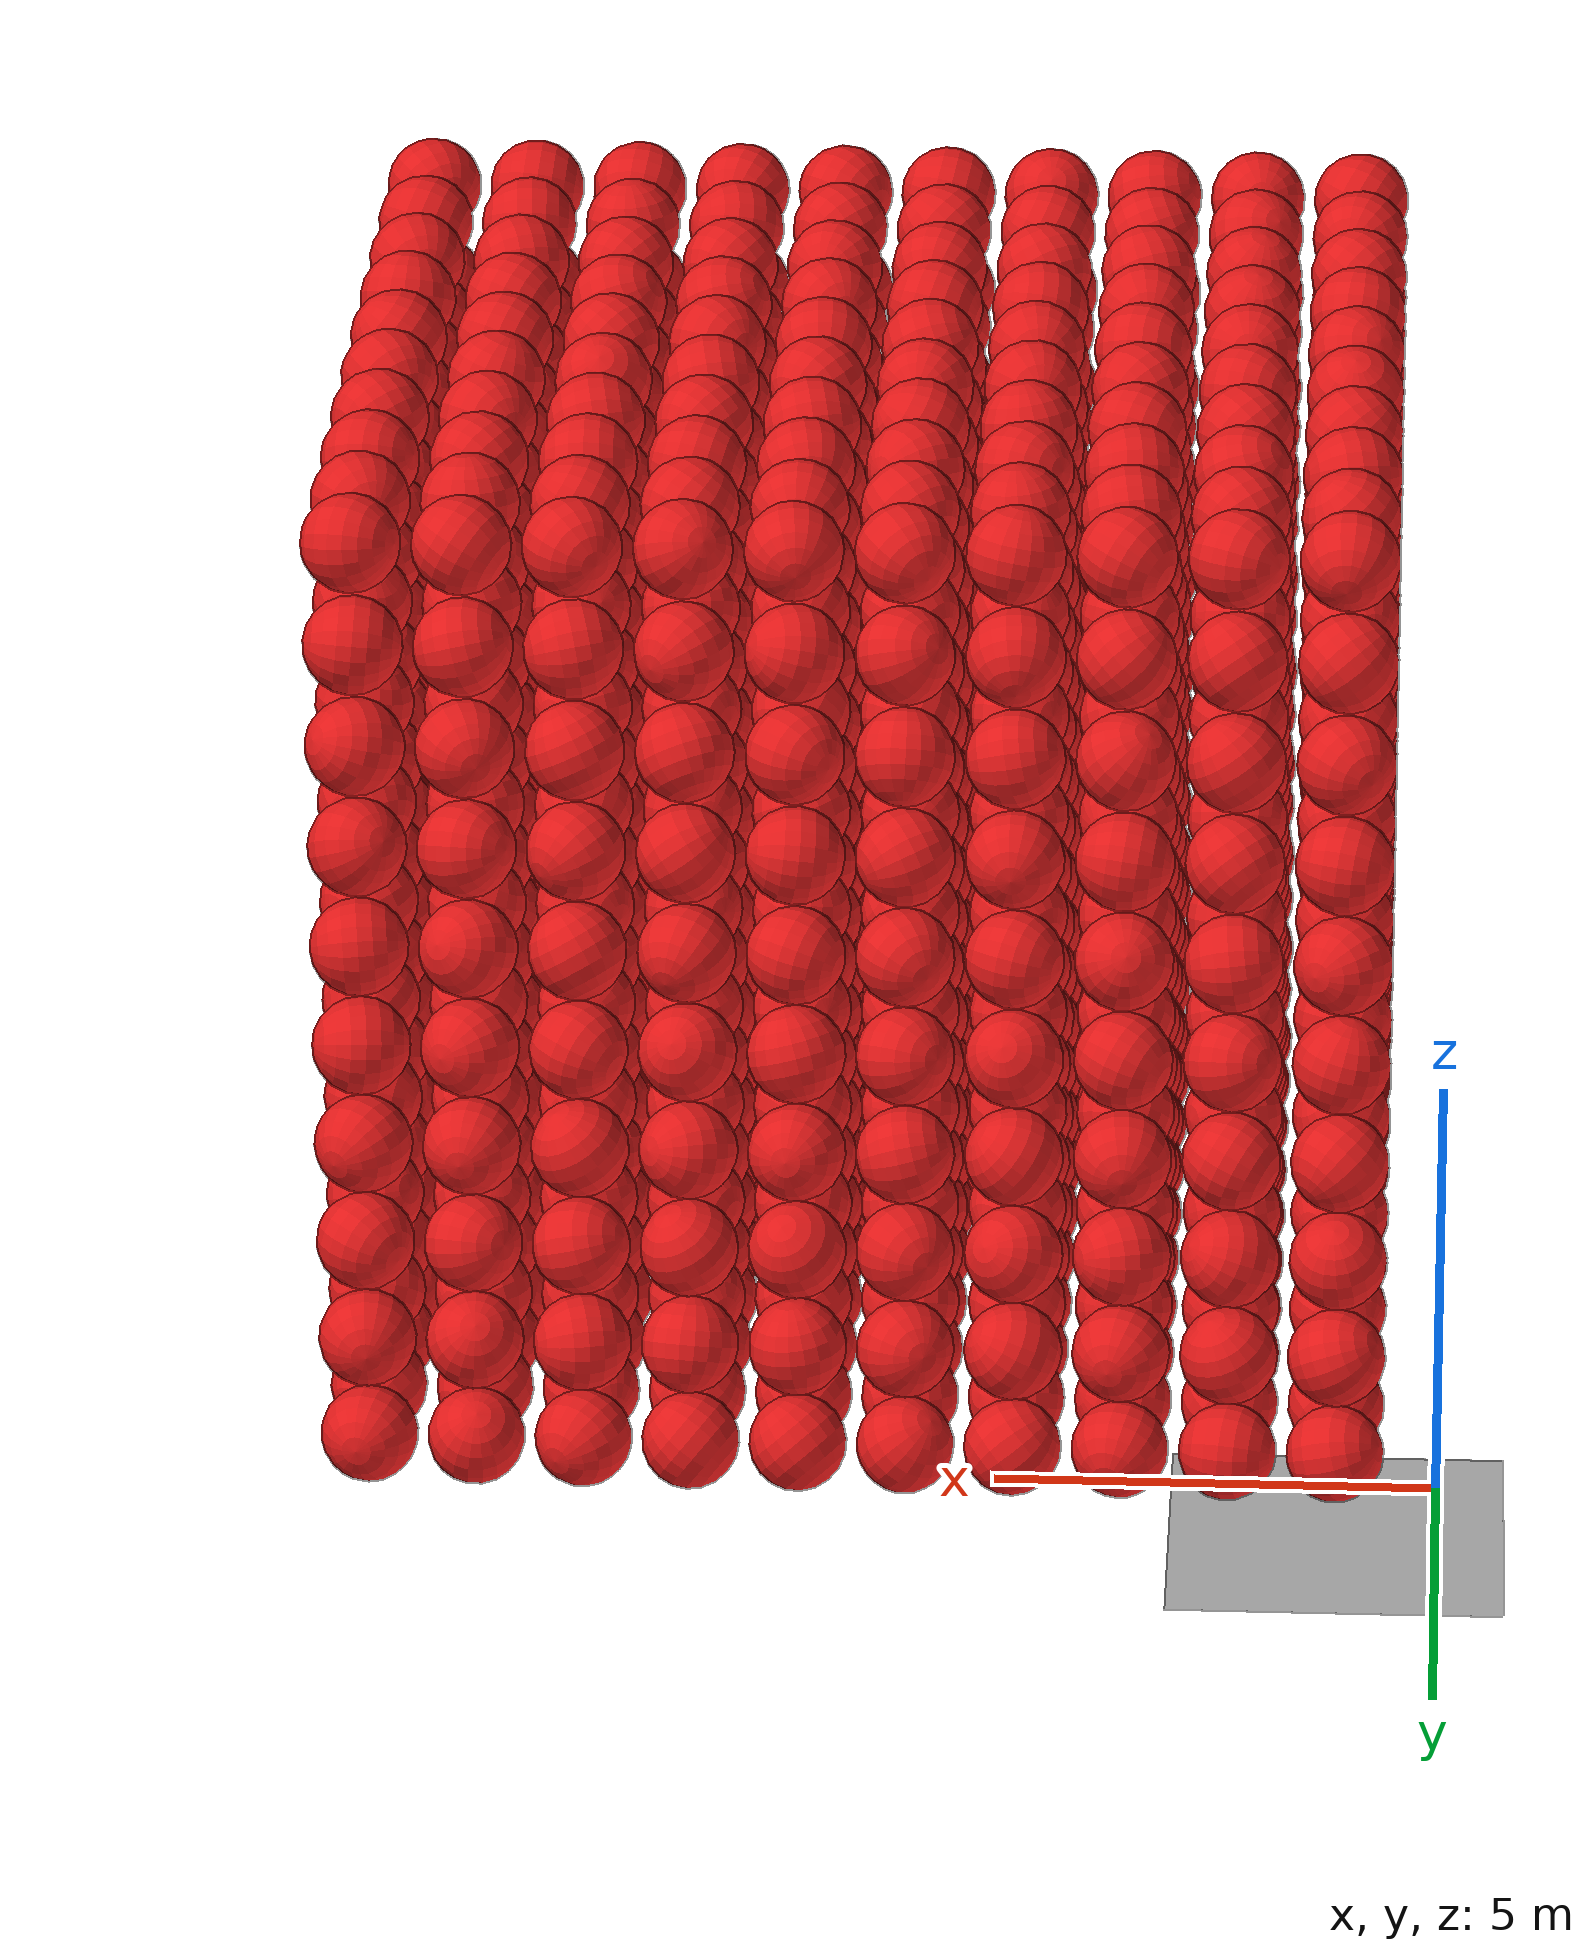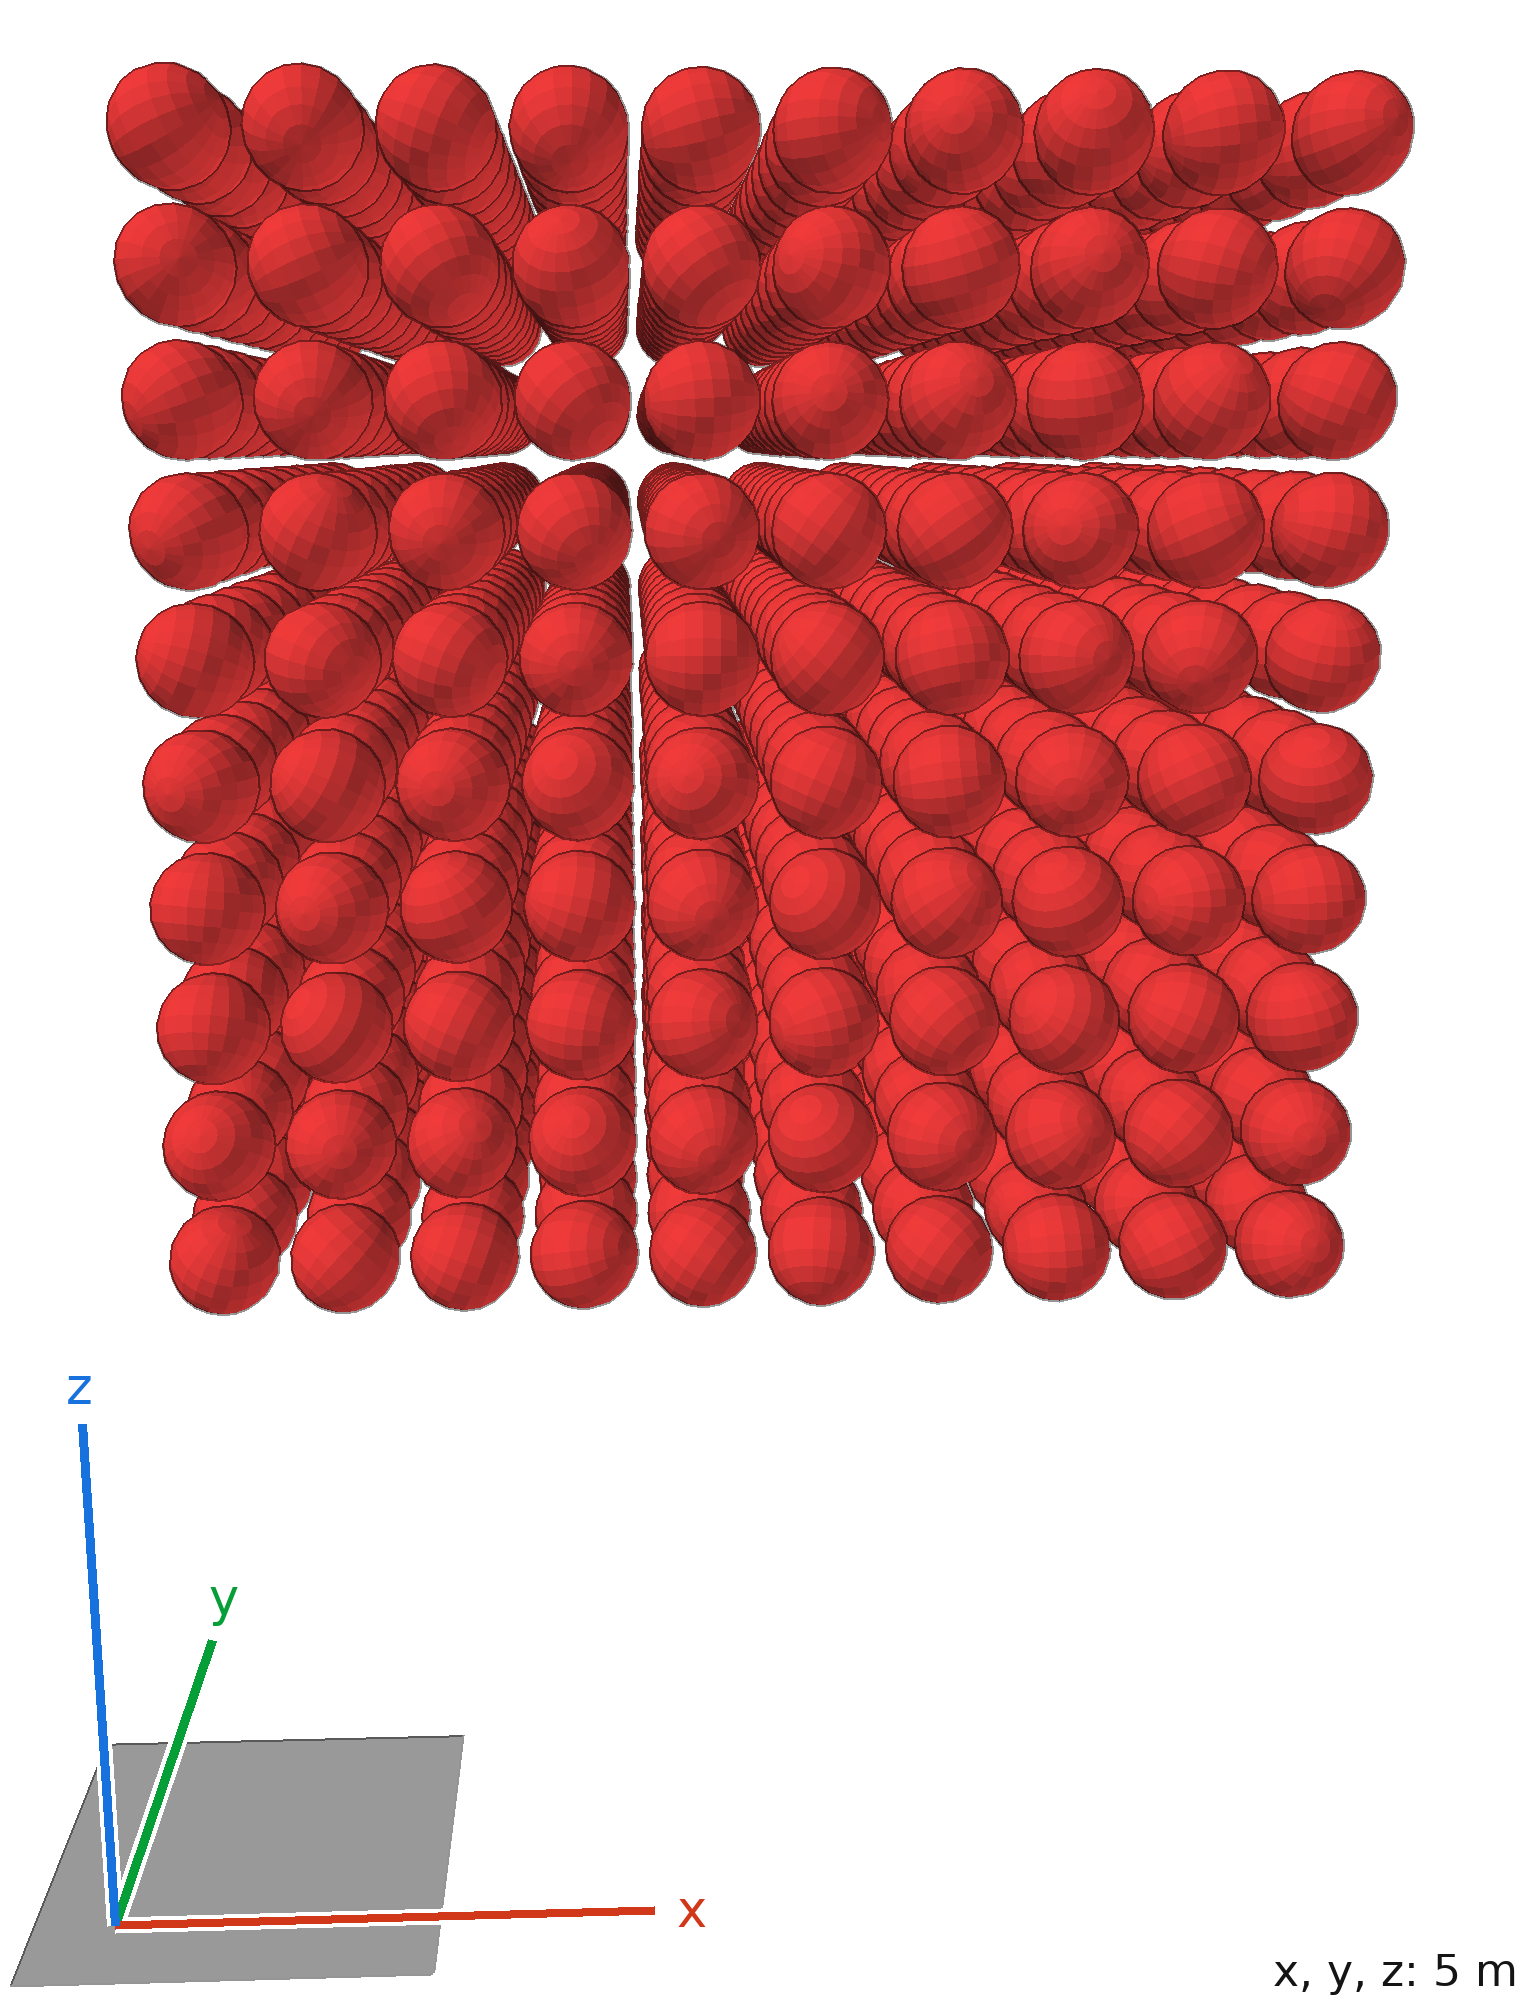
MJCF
<mujoco model="1000 spheres">
    <compiler angle="degree"/>

    <option cone="elliptic"/>

    <size njmax="5000" nconmax="2000" nstack="1000000000"/>

    <default>
        <geom solimp=".9 .9 .01"/>

        <default class="object5">
			<geom type="sphere" material="geom" rgba=".9 .1 .1 1" size="0.500000"/>
        </default>
    </default>

    <asset>
        <texture type="skybox" builtin="gradient" width="128" height="128" rgb1=".4 .6 .8" rgb2="0 0 0"/>
        <texture name="texgeom" type="cube" builtin="flat" mark="cross" width="128" height="128"
            rgb1="0.6 0.6 0.6" rgb2="0.6 0.6 0.6" markrgb="1 1 1"/>
        <texture name="texplane" type="2d" builtin="checker" rgb1=".4 .4 .4" rgb2=".6 .6 .6"
            width="512" height="512"/>
        <material name='geom' texture="texgeom" texuniform="true"/>
        <material name='MatPlane' reflectance='0.3' texture="texplane" texrepeat="1 1" texuniform="true"/>
    </asset>

    <visual>
        <quality shadowsize="4096" offsamples="8"/>
        <map znear="0.1" force="0.05"/>
    </visual>

    <statistic extent="4"/>

    <worldbody>
        <light directional="true" diffuse=".8 .8 .8" pos="0 0 10" dir="0 0 -10"/>

        <geom pos="0 0 0" type="plane" size="3 3 .5" rgba=".7 .7 .7 1" material="MatPlane"/>
		<body pos="1.100672 1.100070 6.100124" quat="-0.243178 0.921006 0.290465 -0.090789"> <freejoint/> <geom class="object5"/> </body>
		<body pos="1.100034 1.100180 7.200932" quat="0.167994 0.011726 -0.521137 0.836694"> <freejoint/> <geom class="object5"/> </body>
		<body pos="1.100362 1.100459 8.300831" quat="0.521347 -0.105784 0.222471 0.817015"> <freejoint/> <geom class="object5"/> </body>
		<body pos="1.100663 1.100266 9.400723" quat="0.118180 0.915177 -0.385294 -0.005765"> <freejoint/> <geom class="object5"/> </body>
		<body pos="1.100284 1.100074 10.500111" quat="-0.588947 0.688099 0.138118 0.400729"> <freejoint/> <geom class="object5"/> </body>
		<body pos="1.100861 1.100827 11.600937" quat="-0.634854 -0.492799 0.308357 0.508946"> <freejoint/> <geom class="object5"/> </body>
		<body pos="1.100374 1.100216 12.700576" quat="-0.597179 -0.574697 0.545684 -0.123814"> <freejoint/> <geom class="object5"/> </body>
		<body pos="1.100785 1.100243 13.800609" quat="0.508844 0.167490 0.548915 0.641652"> <freejoint/> <geom class="object5"/> </body>
		<body pos="1.100150 1.100025 14.900911" quat="-0.528154 -0.615260 0.323632 -0.487617"> <freejoint/> <geom class="object5"/> </body>
		<body pos="1.100160 1.100479 16.000949" quat="0.432966 0.309514 -0.771668 -0.348238"> <freejoint/> <geom class="object5"/> </body>
		<body pos="1.100937 2.200857 6.100891" quat="0.165092 -0.628810 -0.603728 0.461364"> <freejoint/> <geom class="object5"/> </body>
		<body pos="1.100945 2.200658 7.200544" quat="0.189536 -0.515113 0.620642 0.559945"> <freejoint/> <geom class="object5"/> </body>
		<body pos="1.100589 2.200436 8.300550" quat="-0.207317 0.699074 -0.190404 0.657314"> <freejoint/> <geom class="object5"/> </body>
		<body pos="1.100025 2.200778 9.400440" quat="0.235875 -0.336146 0.762421 -0.500084"> <freejoint/> <geom class="object5"/> </body>
		<body pos="1.100374 2.200308 10.500038" quat="0.271277 0.866336 0.227640 -0.352208"> <freejoint/> <geom class="object5"/> </body>
		<body pos="1.100140 2.200117 11.600981" quat="0.074117 -0.735064 -0.433589 -0.515935"> <freejoint/> <geom class="object5"/> </body>
		<body pos="1.100315 2.200904 12.700521" quat="-0.452603 -0.477558 -0.584167 0.475224"> <freejoint/> <geom class="object5"/> </body>
		<body pos="1.100974 2.200929 13.800410" quat="0.768939 -0.029682 -0.058064 -0.635988"> <freejoint/> <geom class="object5"/> </body>
		<body pos="1.100083 2.200633 14.900311" quat="-0.051810 -0.444908 -0.767696 0.458275"> <freejoint/> <geom class="object5"/> </body>
		<body pos="1.100368 2.200015 16.000715" quat="-0.581716 0.390091 -0.525020 -0.483518"> <freejoint/> <geom class="object5"/> </body>
		<body pos="1.100132 3.300344 6.100754" quat="0.759820 0.410786 -0.494898 -0.094891"> <freejoint/> <geom class="object5"/> </body>
		<body pos="1.100931 3.300616 7.200258" quat="0.329144 0.490897 -0.241869 -0.769535"> <freejoint/> <geom class="object5"/> </body>
		<body pos="1.100307 3.300693 8.300630" quat="-0.407512 -0.743721 0.051231 -0.527436"> <freejoint/> <geom class="object5"/> </body>
		<body pos="1.100522 3.300871 9.400614" quat="-0.384621 0.596599 -0.576406 -0.404836"> <freejoint/> <geom class="object5"/> </body>
		<body pos="1.100671 3.300226 10.500826" quat="-0.443776 -0.029299 0.665331 0.599616"> <freejoint/> <geom class="object5"/> </body>
		<body pos="1.100636 3.300249 11.600734" quat="-0.240959 -0.296115 -0.559791 -0.735452"> <freejoint/> <geom class="object5"/> </body>
		<body pos="1.100925 3.300910 12.700382" quat="0.368732 0.315544 -0.681698 -0.547501"> <freejoint/> <geom class="object5"/> </body>
		<body pos="1.100903 3.300892 13.800378" quat="-0.442020 0.181725 0.221978 -0.849894"> <freejoint/> <geom class="object5"/> </body>
		<body pos="1.100820 3.300518 14.900909" quat="-0.458774 0.536694 0.513712 -0.487428"> <freejoint/> <geom class="object5"/> </body>
		<body pos="1.100415 3.300323 16.000846" quat="0.808464 0.413699 0.331814 0.255221"> <freejoint/> <geom class="object5"/> </body>
		<body pos="1.100316 4.400732 6.100158" quat="0.381489 -0.598614 0.685987 0.159839"> <freejoint/> <geom class="object5"/> </body>
		<body pos="1.100895 4.400194 7.200988" quat="-0.537151 -0.574307 -0.203498 0.583292"> <freejoint/> <geom class="object5"/> </body>
		<body pos="1.100839 4.400409 8.300402" quat="0.493077 -0.455201 0.663620 0.330568"> <freejoint/> <geom class="object5"/> </body>
		<body pos="1.100977 4.400186 9.400216" quat="-0.525134 0.707405 -0.371267 0.293211"> <freejoint/> <geom class="object5"/> </body>
		<body pos="1.100383 4.400550 10.500385" quat="0.267157 -0.783677 0.505657 -0.242464"> <freejoint/> <geom class="object5"/> </body>
		<body pos="1.100716 4.400959 11.600507" quat="0.393278 -0.166937 0.827174 0.365031"> <freejoint/> <geom class="object5"/> </body>
		<body pos="1.100504 4.400369 12.700685" quat="-0.553288 -0.624467 0.509863 0.209651"> <freejoint/> <geom class="object5"/> </body>
		<body pos="1.100610 4.400422 13.800504" quat="-0.506131 -0.613080 0.279280 -0.538486"> <freejoint/> <geom class="object5"/> </body>
		<body pos="1.100529 4.400004 14.900425" quat="-0.825199 0.478795 0.009286 0.299526"> <freejoint/> <geom class="object5"/> </body>
		<body pos="1.100200 4.400137 16.000024" quat="0.836329 0.371985 0.103191 -0.389271"> <freejoint/> <geom class="object5"/> </body>
		<body pos="1.100043 5.500854 6.100597" quat="-0.584024 0.525458 -0.594623 0.170978"> <freejoint/> <geom class="object5"/> </body>
		<body pos="1.100789 5.500527 7.200291" quat="0.370793 -0.215351 0.133983 -0.893412"> <freejoint/> <geom class="object5"/> </body>
		<body pos="1.100744 5.500213 8.300100" quat="0.521746 0.424279 0.503843 -0.542135"> <freejoint/> <geom class="object5"/> </body>
		<body pos="1.100700 5.500170 9.400833" quat="0.363455 0.439692 0.419933 -0.705852"> <freejoint/> <geom class="object5"/> </body>
		<body pos="1.100610 5.500898 10.500516" quat="0.011485 -0.454788 0.877636 0.150969"> <freejoint/> <geom class="object5"/> </body>
		<body pos="1.100968 5.500041 11.600189" quat="0.076001 0.541752 -0.612578 0.570505"> <freejoint/> <geom class="object5"/> </body>
		<body pos="1.100355 5.500850 12.700543" quat="0.259855 -0.365472 -0.568507 -0.689714"> <freejoint/> <geom class="object5"/> </body>
		<body pos="1.100888 5.500753 13.800802" quat="-0.096675 -0.700922 -0.570486 -0.417022"> <freejoint/> <geom class="object5"/> </body>
		<body pos="1.100079 5.500853 14.900157" quat="0.277113 0.067578 -0.733457 0.616995"> <freejoint/> <geom class="object5"/> </body>
		<body pos="1.100615 5.500152 16.000455" quat="0.337146 -0.404990 0.231179 0.817846"> <freejoint/> <geom class="object5"/> </body>
		<body pos="1.100567 6.600693 6.100979" quat="0.549489 0.204421 0.664866 -0.462846"> <freejoint/> <geom class="object5"/> </body>
		<body pos="1.100510 6.600627 7.200800" quat="-0.141260 -0.764727 0.032887 -0.627819"> <freejoint/> <geom class="object5"/> </body>
		<body pos="1.100367 6.600697 8.300130" quat="0.397094 -0.624698 0.438444 0.509741"> <freejoint/> <geom class="object5"/> </body>
		<body pos="1.100197 6.600607 9.400997" quat="-0.703195 -0.554990 -0.425713 0.127555"> <freejoint/> <geom class="object5"/> </body>
		<body pos="1.100671 6.600723 10.500504" quat="0.231040 -0.740629 -0.489058 0.398638"> <freejoint/> <geom class="object5"/> </body>
		<body pos="1.100308 6.600749 11.600852" quat="-0.847532 0.206842 0.466666 0.145359"> <freejoint/> <geom class="object5"/> </body>
		<body pos="1.100235 6.600911 12.700951" quat="0.034579 0.438911 0.633278 -0.636490"> <freejoint/> <geom class="object5"/> </body>
		<body pos="1.100107 6.600619 13.800022" quat="-0.668506 -0.556035 0.460713 -0.177956"> <freejoint/> <geom class="object5"/> </body>
		<body pos="1.100229 6.600368 14.900175" quat="0.632439 -0.391205 -0.424004 0.516914"> <freejoint/> <geom class="object5"/> </body>
		<body pos="1.100585 6.600778 16.000360" quat="-0.945204 0.220928 -0.050684 -0.234971"> <freejoint/> <geom class="object5"/> </body>
		<body pos="1.100317 7.700973 6.100258" quat="0.122018 -0.269009 -0.341815 -0.892137"> <freejoint/> <geom class="object5"/> </body>
		<body pos="1.100668 7.700886 7.200421" quat="0.545145 0.681078 -0.188353 -0.451080"> <freejoint/> <geom class="object5"/> </body>
		<body pos="1.100179 7.700306 8.300850" quat="0.048663 0.624277 -0.747218 0.222654"> <freejoint/> <geom class="object5"/> </body>
		<body pos="1.100567 7.700261 9.400002" quat="-0.286757 0.433037 0.532572 0.668294"> <freejoint/> <geom class="object5"/> </body>
		<body pos="1.100008 7.700733 10.500085" quat="0.281590 0.644246 0.696781 0.141950"> <freejoint/> <geom class="object5"/> </body>
		<body pos="1.100260 7.700785 11.600169" quat="-0.309867 -0.679602 -0.140614 -0.649886"> <freejoint/> <geom class="object5"/> </body>
		<body pos="1.100855 7.700205 12.700860" quat="-0.602235 -0.375130 -0.616948 0.340537"> <freejoint/> <geom class="object5"/> </body>
		<body pos="1.100698 7.700919 13.800909" quat="0.448118 0.732887 0.441140 -0.259734"> <freejoint/> <geom class="object5"/> </body>
		<body pos="1.100025 7.700733 14.900473" quat="-0.181476 0.608259 -0.747687 -0.195066"> <freejoint/> <geom class="object5"/> </body>
		<body pos="1.100142 7.700046 16.000698" quat="0.640911 -0.180495 -0.398159 0.630970"> <freejoint/> <geom class="object5"/> </body>
		<body pos="1.100702 8.800896 6.100948" quat="0.634490 0.721804 -0.149737 0.232379"> <freejoint/> <geom class="object5"/> </body>
		<body pos="1.100823 8.800622 7.200701" quat="-0.019484 0.016384 0.519791 -0.853914"> <freejoint/> <geom class="object5"/> </body>
		<body pos="1.100901 8.800732 8.300616" quat="0.542799 -0.458450 -0.624824 0.323708"> <freejoint/> <geom class="object5"/> </body>
		<body pos="1.100928 8.800805 9.400350" quat="-0.427025 0.454537 0.414353 0.662841"> <freejoint/> <geom class="object5"/> </body>
		<body pos="1.100919 8.800269 10.500688" quat="0.208064 -0.755480 -0.549448 -0.289941"> <freejoint/> <geom class="object5"/> </body>
		<body pos="1.100311 8.800420 11.600088" quat="0.129521 0.362645 -0.832266 -0.398805"> <freejoint/> <geom class="object5"/> </body>
		<body pos="1.100981 8.800886 12.700023" quat="0.628259 -0.441003 -0.114828 -0.630573"> <freejoint/> <geom class="object5"/> </body>
		<body pos="1.100216 8.800775 13.800087" quat="-0.258191 0.233541 -0.786521 0.510079"> <freejoint/> <geom class="object5"/> </body>
		<body pos="1.100593 8.800464 14.900241" quat="-0.157112 0.487197 -0.836917 0.193713"> <freejoint/> <geom class="object5"/> </body>
		<body pos="1.100079 8.800415 16.000985" quat="0.476189 -0.622039 0.316188 -0.535104"> <freejoint/> <geom class="object5"/> </body>
		<body pos="1.100485 9.900869 6.100017" quat="0.477238 0.424809 -0.458358 0.617810"> <freejoint/> <geom class="object5"/> </body>
		<body pos="1.100684 9.900888 7.200713" quat="-0.021283 0.469410 -0.576523 -0.668448"> <freejoint/> <geom class="object5"/> </body>
		<body pos="1.100336 9.900487 8.300225" quat="0.099109 0.328164 0.606775 0.717154"> <freejoint/> <geom class="object5"/> </body>
		<body pos="1.100438 9.900400 9.400440" quat="-0.376162 -0.104816 0.917595 -0.074397"> <freejoint/> <geom class="object5"/> </body>
		<body pos="1.100496 9.900022 10.500192" quat="0.671318 -0.186671 -0.671013 -0.253432"> <freejoint/> <geom class="object5"/> </body>
		<body pos="1.100179 9.900249 11.600641" quat="0.543989 0.480997 -0.510188 0.460897"> <freejoint/> <geom class="object5"/> </body>
		<body pos="1.100190 9.900993 12.700326" quat="-0.368087 0.599450 0.419952 0.573421"> <freejoint/> <geom class="object5"/> </body>
		<body pos="1.100719 9.900879 13.800865" quat="-0.269957 -0.688690 0.578978 0.342950"> <freejoint/> <geom class="object5"/> </body>
		<body pos="1.100431 9.900947 14.900951" quat="-0.623736 -0.298369 -0.576184 0.435823"> <freejoint/> <geom class="object5"/> </body>
		<body pos="1.100396 9.900581 16.000344" quat="0.751807 0.164982 0.267469 0.579679"> <freejoint/> <geom class="object5"/> </body>
		<body pos="1.100420 11.000073 6.100871" quat="0.409380 0.718055 0.370665 0.423571"> <freejoint/> <geom class="object5"/> </body>
		<body pos="1.100895 11.000587 7.200325" quat="0.709060 -0.419061 -0.306274 0.477303"> <freejoint/> <geom class="object5"/> </body>
		<body pos="1.100770 11.000201 8.300765" quat="0.242007 0.969225 0.007706 -0.044463"> <freejoint/> <geom class="object5"/> </body>
		<body pos="1.100586 11.000980 9.400349" quat="-0.436231 0.164168 0.447890 -0.762985"> <freejoint/> <geom class="object5"/> </body>
		<body pos="1.100375 11.000087 10.500318" quat="-0.083490 -0.605011 -0.785687 -0.098422"> <freejoint/> <geom class="object5"/> </body>
		<body pos="1.100285 11.000199 11.600510" quat="-0.728539 0.500483 -0.454258 -0.111341"> <freejoint/> <geom class="object5"/> </body>
		<body pos="1.100733 11.000527 12.700269" quat="0.332178 0.563577 -0.474156 -0.589249"> <freejoint/> <geom class="object5"/> </body>
		<body pos="1.100422 11.000064 13.800126" quat="-0.706257 -0.463195 -0.500444 0.190280"> <freejoint/> <geom class="object5"/> </body>
		<body pos="1.100395 11.000727 14.900961" quat="0.398482 -0.670876 0.585982 -0.218544"> <freejoint/> <geom class="object5"/> </body>
		<body pos="1.100797 11.000786 16.000331" quat="0.740942 0.540881 0.212621 -0.336520"> <freejoint/> <geom class="object5"/> </body>
		<body pos="2.200617 1.100989 6.100344" quat="-0.367767 -0.705718 0.578146 0.180158"> <freejoint/> <geom class="object5"/> </body>
		<body pos="2.200786 1.100749 7.200617" quat="-0.589959 0.640262 0.402488 0.282871"> <freejoint/> <geom class="object5"/> </body>
		<body pos="2.200613 1.100874 8.300793" quat="0.395739 -0.160192 0.877535 0.218317"> <freejoint/> <geom class="object5"/> </body>
		<body pos="2.200353 1.100183 9.400321" quat="-0.303869 0.548427 0.488524 0.606824"> <freejoint/> <geom class="object5"/> </body>
		<body pos="2.200952 1.100874 10.500162" quat="-0.548879 0.232723 0.450656 -0.664441"> <freejoint/> <geom class="object5"/> </body>
		<body pos="2.200245 1.100011 11.600233" quat="-0.361074 0.607110 -0.195090 -0.680428"> <freejoint/> <geom class="object5"/> </body>
		<body pos="2.200651 1.100816 12.700084" quat="-0.937775 -0.257969 -0.167458 -0.161209"> <freejoint/> <geom class="object5"/> </body>
		<body pos="2.200463 1.100466 13.800548" quat="0.092741 0.021823 0.797427 -0.595847"> <freejoint/> <geom class="object5"/> </body>
		<body pos="2.200551 1.100575 14.900204" quat="0.105855 -0.547860 0.094203 -0.824481"> <freejoint/> <geom class="object5"/> </body>
		<body pos="2.200860 1.100208 16.000239" quat="-0.303296 -0.540059 0.636293 -0.459869"> <freejoint/> <geom class="object5"/> </body>
		<body pos="2.200107 2.200806 6.100252" quat="0.007973 -0.939577 0.253591 -0.229833"> <freejoint/> <geom class="object5"/> </body>
		<body pos="2.200308 2.200332 7.200932" quat="-0.057305 -0.894967 0.404190 -0.179945"> <freejoint/> <geom class="object5"/> </body>
		<body pos="2.200023 2.200638 8.300439" quat="0.192285 0.247215 -0.096182 -0.944807"> <freejoint/> <geom class="object5"/> </body>
		<body pos="2.200720 2.200740 9.400405" quat="-0.555672 0.554950 0.467475 0.405865"> <freejoint/> <geom class="object5"/> </body>
		<body pos="2.200449 2.200884 10.500854" quat="0.314575 0.014444 -0.902773 -0.292976"> <freejoint/> <geom class="object5"/> </body>
		<body pos="2.200231 2.200860 11.600634" quat="0.373628 -0.554726 0.725840 -0.160742"> <freejoint/> <geom class="object5"/> </body>
		<body pos="2.200611 2.200798 12.700686" quat="-0.585618 0.003113 0.568831 -0.577471"> <freejoint/> <geom class="object5"/> </body>
		<body pos="2.200041 2.200103 13.800603" quat="-0.870306 -0.149832 -0.276423 0.379088"> <freejoint/> <geom class="object5"/> </body>
		<body pos="2.200363 2.200325 14.900677" quat="0.197808 -0.616682 -0.297318 -0.701553"> <freejoint/> <geom class="object5"/> </body>
		<body pos="2.200259 2.200847 16.000427" quat="0.317572 0.063262 0.884076 -0.336981"> <freejoint/> <geom class="object5"/> </body>
		<body pos="2.200361 3.300746 6.100864" quat="-0.714816 0.522748 0.460085 0.063986"> <freejoint/> <geom class="object5"/> </body>
		<body pos="2.200434 3.300602 7.200335" quat="0.498768 -0.723259 -0.086166 0.469790"> <freejoint/> <geom class="object5"/> </body>
		<body pos="2.200626 3.300001 8.300017" quat="-0.136868 -0.883259 -0.407881 -0.186424"> <freejoint/> <geom class="object5"/> </body>
		<body pos="2.200061 3.300364 9.400377" quat="-0.352899 0.742852 -0.040214 -0.567465"> <freejoint/> <geom class="object5"/> </body>
		<body pos="2.200297 3.300829 10.500618" quat="0.336752 0.239192 -0.491407 0.766749"> <freejoint/> <geom class="object5"/> </body>
		<body pos="2.200005 3.300365 11.600592" quat="0.922671 -0.091206 -0.164606 0.336548"> <freejoint/> <geom class="object5"/> </body>
		<body pos="2.200764 3.300380 12.700454" quat="0.344796 0.563833 0.320866 0.678419"> <freejoint/> <geom class="object5"/> </body>
		<body pos="2.200034 3.300101 13.800042" quat="-0.583428 0.575731 0.102143 -0.563659"> <freejoint/> <geom class="object5"/> </body>
		<body pos="2.200939 3.300542 14.900830" quat="-0.477857 -0.699578 0.528736 0.051785"> <freejoint/> <geom class="object5"/> </body>
		<body pos="2.200286 3.300028 16.000153" quat="0.578210 0.038188 -0.169391 -0.797196"> <freejoint/> <geom class="object5"/> </body>
		<body pos="2.200631 4.400127 6.100581" quat="-0.684281 -0.011037 -0.356909 -0.635810"> <freejoint/> <geom class="object5"/> </body>
		<body pos="2.200105 4.400154 7.200873" quat="0.331598 -0.733652 0.458762 -0.375944"> <freejoint/> <geom class="object5"/> </body>
		<body pos="2.200886 4.400839 8.300356" quat="-0.409026 -0.765600 -0.247021 -0.430738"> <freejoint/> <geom class="object5"/> </body>
		<body pos="2.200821 4.400280 9.400851" quat="-0.800409 -0.380872 -0.404583 0.224932"> <freejoint/> <geom class="object5"/> </body>
		<body pos="2.200456 4.400038 10.500380" quat="0.079176 -0.735335 -0.488427 0.463091"> <freejoint/> <geom class="object5"/> </body>
		<body pos="2.200630 4.400809 11.600021" quat="-0.836557 -0.173402 -0.497408 0.150633"> <freejoint/> <geom class="object5"/> </body>
		<body pos="2.200823 4.400749 12.700929" quat="0.059900 0.094308 0.408256 0.906005"> <freejoint/> <geom class="object5"/> </body>
		<body pos="2.200181 4.400699 13.800189" quat="-0.468960 0.423315 0.046705 -0.773757"> <freejoint/> <geom class="object5"/> </body>
		<body pos="2.200955 4.400877 14.900872" quat="-0.011244 0.058530 -0.880240 0.470771"> <freejoint/> <geom class="object5"/> </body>
		<body pos="2.200758 4.400584 16.000370" quat="-0.022077 0.075014 -0.141502 -0.986845"> <freejoint/> <geom class="object5"/> </body>
		<body pos="2.200653 5.500675 6.100750" quat="-0.412511 0.646901 -0.425177 -0.480186"> <freejoint/> <geom class="object5"/> </body>
		<body pos="2.200270 5.500763 7.200319" quat="-0.228592 0.280524 -0.745683 -0.559472"> <freejoint/> <geom class="object5"/> </body>
		<body pos="2.200422 5.500213 8.300760" quat="0.302062 0.715909 -0.615910 -0.129951"> <freejoint/> <geom class="object5"/> </body>
		<body pos="2.200732 5.500105 9.400445" quat="-0.016145 0.332264 0.736228 -0.589329"> <freejoint/> <geom class="object5"/> </body>
		<body pos="2.200053 5.500609 10.500243" quat="0.235144 0.719926 -0.135092 0.638877"> <freejoint/> <geom class="object5"/> </body>
		<body pos="2.200808 5.500856 11.600711" quat="-0.521246 -0.449064 -0.691910 0.218872"> <freejoint/> <geom class="object5"/> </body>
		<body pos="2.200778 5.500096 12.700410" quat="0.242359 0.489928 0.028819 -0.836900"> <freejoint/> <geom class="object5"/> </body>
		<body pos="2.200441 5.500781 13.800991" quat="0.528161 -0.665365 0.403328 0.340092"> <freejoint/> <geom class="object5"/> </body>
		<body pos="2.200755 5.500201 14.900324" quat="0.198395 0.975053 -0.099263 -0.007550"> <freejoint/> <geom class="object5"/> </body>
		<body pos="2.200972 5.500763 16.000980" quat="-0.432191 -0.681123 -0.497176 0.319528"> <freejoint/> <geom class="object5"/> </body>
		<body pos="2.200777 6.600645 6.100338" quat="0.213842 -0.628234 0.508131 -0.548996"> <freejoint/> <geom class="object5"/> </body>
		<body pos="2.200947 6.600379 7.200135" quat="-0.308866 0.658079 0.463481 -0.506675"> <freejoint/> <geom class="object5"/> </body>
		<body pos="2.200174 6.600893 8.300771" quat="0.549179 -0.538511 -0.576459 0.275869"> <freejoint/> <geom class="object5"/> </body>
		<body pos="2.200111 6.600506 9.400685" quat="-0.544811 -0.201144 0.489849 0.650207"> <freejoint/> <geom class="object5"/> </body>
		<body pos="2.200161 6.600738 10.500556" quat="-0.714028 0.434658 -0.457920 0.302563"> <freejoint/> <geom class="object5"/> </body>
		<body pos="2.200236 6.600489 11.600758" quat="0.333174 -0.699080 0.424640 -0.469003"> <freejoint/> <geom class="object5"/> </body>
		<body pos="2.200119 6.600657 12.700947" quat="0.619210 -0.641821 0.340307 0.298054"> <freejoint/> <geom class="object5"/> </body>
		<body pos="2.200510 6.600435 13.800384" quat="0.719311 -0.523606 -0.438193 0.128122"> <freejoint/> <geom class="object5"/> </body>
		<body pos="2.200627 6.600450 14.900864" quat="0.643573 0.448739 0.311983 -0.535830"> <freejoint/> <geom class="object5"/> </body>
		<body pos="2.200083 6.600839 16.000351" quat="0.602693 0.115731 -0.666993 -0.422479"> <freejoint/> <geom class="object5"/> </body>
		<body pos="2.200147 7.700416 6.100878" quat="-0.527487 0.557039 0.564805 -0.304074"> <freejoint/> <geom class="object5"/> </body>
		<body pos="2.200036 7.700466 7.200584" quat="0.348674 -0.256045 -0.670949 0.602242"> <freejoint/> <geom class="object5"/> </body>
		<body pos="2.200829 7.700373 8.300765" quat="-0.232259 0.067793 0.223317 -0.944240"> <freejoint/> <geom class="object5"/> </body>
		<body pos="2.200128 7.700610 9.400614" quat="-0.377725 0.509597 -0.548193 0.545086"> <freejoint/> <geom class="object5"/> </body>
		<body pos="2.200389 7.700300 10.500753" quat="-0.411347 0.044752 -0.474293 -0.777069"> <freejoint/> <geom class="object5"/> </body>
		<body pos="2.200828 7.700116 11.600542" quat="0.158490 -0.635087 -0.427589 -0.623468"> <freejoint/> <geom class="object5"/> </body>
		<body pos="2.200753 7.700704 12.700356" quat="0.307899 -0.738986 0.582970 -0.138725"> <freejoint/> <geom class="object5"/> </body>
		<body pos="2.200102 7.700098 13.800106" quat="0.262232 -0.660584 -0.169672 0.682697"> <freejoint/> <geom class="object5"/> </body>
		<body pos="2.200329 7.700273 14.900819" quat="-0.847746 0.446400 0.219531 0.184007"> <freejoint/> <geom class="object5"/> </body>
		<body pos="2.200315 7.700146 16.000130" quat="0.660643 -0.048947 -0.517273 0.541834"> <freejoint/> <geom class="object5"/> </body>
		<body pos="2.200682 8.800161 6.100141" quat="0.406341 0.382237 0.346292 -0.754230"> <freejoint/> <geom class="object5"/> </body>
		<body pos="2.200822 8.800614 7.200932" quat="0.226321 -0.351641 -0.635580 -0.648973"> <freejoint/> <geom class="object5"/> </body>
		<body pos="2.200718 8.800243 8.300146" quat="-0.649767 0.440017 0.485459 -0.385380"> <freejoint/> <geom class="object5"/> </body>
		<body pos="2.200748 8.800282 9.400338" quat="-0.271477 -0.688835 -0.672115 -0.008215"> <freejoint/> <geom class="object5"/> </body>
		<body pos="2.200376 8.800417 10.500620" quat="0.452601 0.375049 -0.442274 0.677410"> <freejoint/> <geom class="object5"/> </body>
		<body pos="2.200696 8.800587 11.600883" quat="0.724973 0.570959 -0.284842 0.259393"> <freejoint/> <geom class="object5"/> </body>
		<body pos="2.200906 8.800685 12.700999" quat="-0.001048 -0.392945 0.334652 0.856505"> <freejoint/> <geom class="object5"/> </body>
		<body pos="2.200210 8.800416 13.800162" quat="-0.470370 -0.199765 -0.300389 0.805365"> <freejoint/> <geom class="object5"/> </body>
		<body pos="2.200453 8.800527 14.900501" quat="0.525075 0.515789 -0.646651 0.200250"> <freejoint/> <geom class="object5"/> </body>
		<body pos="2.200773 8.800285 16.000269" quat="-0.228580 -0.868547 -0.140043 -0.416852"> <freejoint/> <geom class="object5"/> </body>
		<body pos="2.200255 9.900141 6.100266" quat="-0.268171 -0.438015 -0.853597 -0.087173"> <freejoint/> <geom class="object5"/> </body>
		<body pos="2.200905 9.900657 7.200143" quat="-0.441463 0.532426 0.415646 0.590654"> <freejoint/> <geom class="object5"/> </body>
		<body pos="2.200936 9.900191 8.300527" quat="-0.577159 -0.241009 -0.684380 -0.374735"> <freejoint/> <geom class="object5"/> </body>
		<body pos="2.200164 9.900003 9.400407" quat="-0.481916 -0.705711 0.187311 0.484400"> <freejoint/> <geom class="object5"/> </body>
		<body pos="2.200721 9.900509 10.500326" quat="-0.089053 -0.400520 0.360901 0.837499"> <freejoint/> <geom class="object5"/> </body>
		<body pos="2.200292 9.900476 11.600392" quat="-0.289742 -0.159689 0.604096 0.724994"> <freejoint/> <geom class="object5"/> </body>
		<body pos="2.200004 9.900601 12.700786" quat="0.227096 -0.627944 0.345157 -0.659531"> <freejoint/> <geom class="object5"/> </body>
		<body pos="2.200585 9.900848 13.800231" quat="-0.381253 -0.579597 0.410767 -0.591594"> <freejoint/> <geom class="object5"/> </body>
		<body pos="2.200367 9.900175 14.900504" quat="-0.008085 0.735006 0.143301 -0.662696"> <freejoint/> <geom class="object5"/> </body>
		<body pos="2.200908 9.900664 16.000503" quat="0.593073 -0.390925 0.701492 0.057889"> <freejoint/> <geom class="object5"/> </body>
		<body pos="2.200093 11.000484 6.100322" quat="0.064063 0.679138 -0.196997 -0.704173"> <freejoint/> <geom class="object5"/> </body>
		<body pos="2.200740 11.000325 7.200665" quat="-0.004814 0.799444 0.555705 -0.228163"> <freejoint/> <geom class="object5"/> </body>
		<body pos="2.200514 11.000584 8.300508" quat="0.519661 0.507927 -0.679644 -0.100229"> <freejoint/> <geom class="object5"/> </body>
		<body pos="2.200519 11.000149 9.400782" quat="-0.778316 -0.011111 -0.560240 0.283252"> <freejoint/> <geom class="object5"/> </body>
		<body pos="2.200457 11.000255 10.500534" quat="-0.693907 0.104555 0.598450 0.386547"> <freejoint/> <geom class="object5"/> </body>
		<body pos="2.200539 11.000672 11.600861" quat="0.094339 0.746100 0.103099 0.651003"> <freejoint/> <geom class="object5"/> </body>
		<body pos="2.200453 11.000161 12.700237" quat="0.357477 -0.212030 0.342800 -0.842462"> <freejoint/> <geom class="object5"/> </body>
		<body pos="2.200934 11.000703 13.800676" quat="-0.202564 0.280912 -0.096641 0.933122"> <freejoint/> <geom class="object5"/> </body>
		<body pos="2.200094 11.000468 14.900694" quat="0.889319 0.264715 0.235738 0.288904"> <freejoint/> <geom class="object5"/> </body>
		<body pos="2.200152 11.000245 16.000550" quat="-0.602379 0.009463 0.701481 0.380754"> <freejoint/> <geom class="object5"/> </body>
		<body pos="3.300037 1.100208 6.100403" quat="0.778306 0.200963 -0.524220 -0.281155"> <freejoint/> <geom class="object5"/> </body>
		<body pos="3.300268 1.100385 7.200878" quat="0.211109 -0.671759 0.569874 0.423576"> <freejoint/> <geom class="object5"/> </body>
		<body pos="3.300089 1.100367 8.300940" quat="0.695128 -0.393163 -0.387054 0.460879"> <freejoint/> <geom class="object5"/> </body>
		<body pos="3.300402 1.100886 9.400452" quat="-0.016862 -0.711308 -0.662328 -0.234686"> <freejoint/> <geom class="object5"/> </body>
		<body pos="3.300718 1.100730 10.500336" quat="-0.053861 -0.184497 -0.657840 0.728221"> <freejoint/> <geom class="object5"/> </body>
		<body pos="3.300596 1.100450 11.600972" quat="0.765228 -0.048742 -0.578637 -0.277901"> <freejoint/> <geom class="object5"/> </body>
		<body pos="3.300206 1.100545 12.700958" quat="-0.465798 0.402118 0.502089 0.607651"> <freejoint/> <geom class="object5"/> </body>
		<body pos="3.300631 1.100594 13.800773" quat="-0.384627 -0.833491 -0.392508 0.057380"> <freejoint/> <geom class="object5"/> </body>
		<body pos="3.300225 1.100912 14.900113" quat="-0.530815 -0.045899 0.365604 0.763192"> <freejoint/> <geom class="object5"/> </body>
		<body pos="3.300635 1.100807 16.000572" quat="-0.015184 0.552356 -0.107990 -0.826445"> <freejoint/> <geom class="object5"/> </body>
		<body pos="3.300987 2.200749 6.100579" quat="-0.295404 0.166291 0.715462 0.610899"> <freejoint/> <geom class="object5"/> </body>
		<body pos="3.300868 2.200104 7.200787" quat="-0.167665 -0.344165 -0.844182 0.375228"> <freejoint/> <geom class="object5"/> </body>
		<body pos="3.300844 2.200050 8.300246" quat="0.586888 -0.508354 0.597081 -0.201577"> <freejoint/> <geom class="object5"/> </body>
		<body pos="3.300880 2.200276 9.400714" quat="-0.642207 -0.560145 0.512002 -0.107995"> <freejoint/> <geom class="object5"/> </body>
		<body pos="3.300563 2.200733 10.500961" quat="-0.585462 -0.505210 -0.490292 0.402008"> <freejoint/> <geom class="object5"/> </body>
		<body pos="3.300160 2.200526 11.600709" quat="0.897266 0.202061 -0.381337 0.093094"> <freejoint/> <geom class="object5"/> </body>
		<body pos="3.300541 2.200901 12.700071" quat="0.613943 0.514878 0.557138 0.218113"> <freejoint/> <geom class="object5"/> </body>
		<body pos="3.300727 2.200093 13.800135" quat="0.468930 0.521235 -0.599333 0.386288"> <freejoint/> <geom class="object5"/> </body>
		<body pos="3.300321 2.200238 14.900840" quat="-0.142185 0.289523 -0.840235 0.435850"> <freejoint/> <geom class="object5"/> </body>
		<body pos="3.300998 2.200384 16.000529" quat="0.453873 -0.539540 0.641155 -0.303012"> <freejoint/> <geom class="object5"/> </body>
		<body pos="3.300679 3.300459 6.100664" quat="0.394908 -0.556355 0.094420 -0.724984"> <freejoint/> <geom class="object5"/> </body>
		<body pos="3.300907 3.300573 7.200845" quat="0.704250 0.438756 0.080128 0.552363"> <freejoint/> <geom class="object5"/> </body>
		<body pos="3.300268 3.300941 8.300990" quat="0.658267 -0.729914 0.135606 -0.124586"> <freejoint/> <geom class="object5"/> </body>
		<body pos="3.300046 3.300925 9.400751" quat="-0.619229 0.312901 -0.300976 0.654264"> <freejoint/> <geom class="object5"/> </body>
		<body pos="3.300149 3.300597 10.500465" quat="-0.184810 0.793089 -0.573442 0.089550"> <freejoint/> <geom class="object5"/> </body>
		<body pos="3.300948 3.300653 11.600034" quat="-0.233998 0.787232 -0.235142 0.519826"> <freejoint/> <geom class="object5"/> </body>
		<body pos="3.300741 3.300230 12.700924" quat="-0.601123 0.605327 -0.163415 0.495506"> <freejoint/> <geom class="object5"/> </body>
		<body pos="3.300340 3.300891 13.800855" quat="-0.672520 0.333186 -0.640224 -0.163759"> <freejoint/> <geom class="object5"/> </body>
		<body pos="3.300550 3.300552 14.900773" quat="0.496296 0.840405 -0.074799 -0.204490"> <freejoint/> <geom class="object5"/> </body>
		<body pos="3.300944 3.300096 16.000559" quat="-0.367740 0.895704 0.239452 -0.071722"> <freejoint/> <geom class="object5"/> </body>
		<body pos="3.300879 4.400733 6.100589" quat="-0.532282 -0.637266 -0.554071 -0.059775"> <freejoint/> <geom class="object5"/> </body>
		<body pos="3.300188 4.400075 7.200329" quat="-0.479885 -0.286525 0.092290 0.824073"> <freejoint/> <geom class="object5"/> </body>
		<body pos="3.300227 4.400400 8.300991" quat="-0.055146 0.703503 -0.002265 0.708546"> <freejoint/> <geom class="object5"/> </body>
		<body pos="3.300538 4.400133 9.400339" quat="0.351449 -0.129458 0.651801 -0.659454"> <freejoint/> <geom class="object5"/> </body>
		<body pos="3.300379 4.400565 10.500757" quat="0.408818 -0.207772 0.707981 -0.537086"> <freejoint/> <geom class="object5"/> </body>
		<body pos="3.300890 4.400258 11.600414" quat="-0.916011 0.084528 -0.285825 0.268481"> <freejoint/> <geom class="object5"/> </body>
		<body pos="3.300932 4.400588 12.700261" quat="0.557819 -0.673314 -0.379478 0.302460"> <freejoint/> <geom class="object5"/> </body>
		<body pos="3.300100 4.400717 13.800240" quat="-0.190438 -0.460052 -0.761178 -0.415564"> <freejoint/> <geom class="object5"/> </body>
		<body pos="3.300633 4.400023 14.900624" quat="-0.686606 -0.235754 -0.078252 0.683277"> <freejoint/> <geom class="object5"/> </body>
		<body pos="3.300221 4.400382 16.000907" quat="-0.576848 -0.697730 0.290789 -0.309615"> <freejoint/> <geom class="object5"/> </body>
		<body pos="3.300997 5.500184 6.100555" quat="0.252918 -0.002668 -0.103718 -0.961909"> <freejoint/> <geom class="object5"/> </body>
		<body pos="3.300259 5.500722 7.200996" quat="0.108175 0.281005 0.353620 0.885600"> <freejoint/> <geom class="object5"/> </body>
		<body pos="3.300366 5.500469 8.300129" quat="-0.735727 0.077055 0.301696 0.601455"> <freejoint/> <geom class="object5"/> </body>
		<body pos="3.300598 5.500062 9.400738" quat="-0.422710 -0.506270 -0.550321 -0.512010"> <freejoint/> <geom class="object5"/> </body>
		<body pos="3.300213 5.500389 10.500288" quat="-0.596522 0.227883 -0.657863 0.399309"> <freejoint/> <geom class="object5"/> </body>
		<body pos="3.300890 5.500443 11.600408" quat="-0.159928 0.703048 0.050526 -0.691082"> <freejoint/> <geom class="object5"/> </body>
		<body pos="3.300212 5.500168 12.700355" quat="-0.301962 0.115211 -0.821910 0.469052"> <freejoint/> <geom class="object5"/> </body>
		<body pos="3.300355 5.500647 13.800425" quat="0.435008 -0.434502 -0.526664 -0.587027"> <freejoint/> <geom class="object5"/> </body>
		<body pos="3.300991 5.500975 14.900922" quat="-0.119556 -0.732105 -0.305494 0.596995"> <freejoint/> <geom class="object5"/> </body>
		<body pos="3.300901 5.500860 16.000973" quat="-0.540345 -0.584298 -0.474760 -0.375799"> <freejoint/> <geom class="object5"/> </body>
		<body pos="3.300728 6.600223 6.100597" quat="-0.638919 0.147464 -0.080410 0.750714"> <freejoint/> <geom class="object5"/> </body>
		<body pos="3.300007 6.600367 7.200163" quat="-0.718449 0.680199 -0.122268 0.078807"> <freejoint/> <geom class="object5"/> </body>
		<body pos="3.300087 6.600589 8.300408" quat="0.171660 -0.700883 -0.689262 -0.064923"> <freejoint/> <geom class="object5"/> </body>
		<body pos="3.300820 6.600699 9.400550" quat="-0.495752 0.228731 -0.753671 0.365913"> <freejoint/> <geom class="object5"/> </body>
		<body pos="3.300424 6.600516 10.500911" quat="0.424448 0.785658 0.437611 -0.105268"> <freejoint/> <geom class="object5"/> </body>
		<body pos="3.300455 6.600512 11.600234" quat="-0.161182 -0.950797 0.062503 -0.257099"> <freejoint/> <geom class="object5"/> </body>
		<body pos="3.300055 6.600364 12.700099" quat="0.312500 -0.786015 0.229231 -0.481641"> <freejoint/> <geom class="object5"/> </body>
		<body pos="3.300746 6.600782 13.800119" quat="-0.127903 -0.657307 -0.742257 0.025346"> <freejoint/> <geom class="object5"/> </body>
		<body pos="3.300185 6.600725 14.900039" quat="-0.499037 0.535734 0.506959 -0.454912"> <freejoint/> <geom class="object5"/> </body>
		<body pos="3.300488 6.600535 16.000196" quat="0.613537 -0.321779 0.668140 0.271328"> <freejoint/> <geom class="object5"/> </body>
		<body pos="3.300618 7.700549 6.100778" quat="-0.421866 -0.606256 -0.231754 -0.633066"> <freejoint/> <geom class="object5"/> </body>
		<body pos="3.300381 7.700978 7.200614" quat="0.539552 -0.357374 -0.385363 -0.657772"> <freejoint/> <geom class="object5"/> </body>
		<body pos="3.300899 7.700416 8.300680" quat="-0.587274 -0.407419 -0.513931 -0.474335"> <freejoint/> <geom class="object5"/> </body>
		<body pos="3.300189 7.700465 9.400172" quat="0.043592 0.362939 0.763784 0.531986"> <freejoint/> <geom class="object5"/> </body>
		<body pos="3.300984 7.700220 10.500173" quat="0.607281 0.573103 -0.176415 -0.521192"> <freejoint/> <geom class="object5"/> </body>
		<body pos="3.300142 7.700007 11.600808" quat="0.590667 0.754608 -0.274701 -0.078856"> <freejoint/> <geom class="object5"/> </body>
		<body pos="3.300646 7.700674 12.700976" quat="0.143174 0.540256 0.540789 0.628627"> <freejoint/> <geom class="object5"/> </body>
		<body pos="3.300268 7.700946 13.800112" quat="0.541800 -0.571858 0.583295 0.197986"> <freejoint/> <geom class="object5"/> </body>
		<body pos="3.300601 7.700468 14.900514" quat="0.124244 0.527930 0.174905 -0.821743"> <freejoint/> <geom class="object5"/> </body>
		<body pos="3.300375 7.700631 16.000515" quat="-0.592162 0.526137 0.541501 -0.281603"> <freejoint/> <geom class="object5"/> </body>
		<body pos="3.300158 8.800857 6.100317" quat="-0.400856 0.627489 0.524151 -0.413325"> <freejoint/> <geom class="object5"/> </body>
		<body pos="3.300899 8.800126 7.200857" quat="0.500793 -0.071138 -0.573560 -0.644341"> <freejoint/> <geom class="object5"/> </body>
		<body pos="3.300174 8.800727 8.300487" quat="0.011089 0.672479 -0.455639 -0.583132"> <freejoint/> <geom class="object5"/> </body>
		<body pos="3.300442 8.800222 9.400236" quat="-0.408411 -0.658035 -0.588462 -0.232171"> <freejoint/> <geom class="object5"/> </body>
		<body pos="3.300987 8.800859 10.500734" quat="0.146789 -0.427026 -0.421148 -0.786598"> <freejoint/> <geom class="object5"/> </body>
		<body pos="3.300816 8.800713 11.600775" quat="-0.388232 0.567039 0.016375 -0.726275"> <freejoint/> <geom class="object5"/> </body>
		<body pos="3.300876 8.800205 12.700292" quat="-0.353904 0.635271 -0.573628 0.377006"> <freejoint/> <geom class="object5"/> </body>
		<body pos="3.300806 8.800742 13.800792" quat="0.359588 0.506060 -0.245058 0.744678"> <freejoint/> <geom class="object5"/> </body>
		<body pos="3.300553 8.800856 14.900958" quat="0.915992 -0.246304 0.309031 0.069236"> <freejoint/> <geom class="object5"/> </body>
		<body pos="3.300608 8.800176 16.000518" quat="-0.006617 0.721715 0.151772 -0.675314"> <freejoint/> <geom class="object5"/> </body>
		<body pos="3.300130 9.900657 6.100213" quat="-0.150958 0.678124 0.457754 -0.554816"> <freejoint/> <geom class="object5"/> </body>
		<body pos="3.300773 9.900355 7.200090" quat="0.395509 0.376949 -0.729344 0.411752"> <freejoint/> <geom class="object5"/> </body>
		<body pos="3.300084 9.900892 8.300888" quat="0.116896 0.585064 -0.629457 -0.497814"> <freejoint/> <geom class="object5"/> </body>
		<body pos="3.300049 9.900692 9.400293" quat="0.477423 0.066916 -0.331466 0.810999"> <freejoint/> <geom class="object5"/> </body>
		<body pos="3.300828 9.900523 10.500123" quat="-0.593613 0.251856 0.306418 0.700214"> <freejoint/> <geom class="object5"/> </body>
		<body pos="3.300962 9.900402 11.600187" quat="-0.256512 0.892829 0.220750 0.297199"> <freejoint/> <geom class="object5"/> </body>
		<body pos="3.300961 9.900240 12.700318" quat="-0.289970 0.566947 0.418480 0.647582"> <freejoint/> <geom class="object5"/> </body>
		<body pos="3.300173 9.900805 13.800364" quat="0.174438 -0.596498 0.616488 -0.483429"> <freejoint/> <geom class="object5"/> </body>
		<body pos="3.300677 9.900834 14.900043" quat="0.652636 -0.517144 -0.510583 0.214322"> <freejoint/> <geom class="object5"/> </body>
		<body pos="3.300330 9.900978 16.000663" quat="0.515746 -0.441530 -0.491325 0.545579"> <freejoint/> <geom class="object5"/> </body>
		<body pos="3.300735 11.000023 6.100108" quat="-0.563423 -0.313072 0.520556 -0.559965"> <freejoint/> <geom class="object5"/> </body>
		<body pos="3.300574 11.000922 7.200978" quat="0.632668 -0.702954 -0.136958 -0.294668"> <freejoint/> <geom class="object5"/> </body>
		<body pos="3.300423 11.000915 8.300285" quat="0.134985 0.552083 0.393748 0.722458"> <freejoint/> <geom class="object5"/> </body>
		<body pos="3.300055 11.000860 9.400008" quat="0.377089 0.364994 -0.561529 0.639741"> <freejoint/> <geom class="object5"/> </body>
		<body pos="3.300157 11.000912 10.500234" quat="0.400648 0.301249 -0.737315 -0.452877"> <freejoint/> <geom class="object5"/> </body>
		<body pos="3.300199 11.000932 11.600541" quat="0.726922 -0.453819 0.232956 0.459743"> <freejoint/> <geom class="object5"/> </body>
		<body pos="3.300400 11.000837 12.700163" quat="-0.664894 -0.349652 -0.562216 -0.345793"> <freejoint/> <geom class="object5"/> </body>
		<body pos="3.300986 11.000624 13.800596" quat="0.251555 -0.315586 0.147910 0.902911"> <freejoint/> <geom class="object5"/> </body>
		<body pos="3.300470 11.000088 14.900934" quat="-0.680228 0.221619 0.347301 -0.606265"> <freejoint/> <geom class="object5"/> </body>
		<body pos="3.300786 11.000925 16.000564" quat="-0.074498 0.477959 -0.352069 0.801281"> <freejoint/> <geom class="object5"/> </body>
		<body pos="4.400986 1.100536 6.100894" quat="-0.515348 -0.041886 0.794253 0.319100"> <freejoint/> <geom class="object5"/> </body>
		<body pos="4.400436 1.100854 7.200396" quat="-0.075706 -0.120572 -0.424443 0.894192"> <freejoint/> <geom class="object5"/> </body>
		<body pos="4.400883 1.100343 8.300954" quat="-0.258479 0.586199 -0.459302 0.615305"> <freejoint/> <geom class="object5"/> </body>
		<body pos="4.400879 1.100507 9.400018" quat="0.588907 -0.297556 0.737946 -0.141721"> <freejoint/> <geom class="object5"/> </body>
		<body pos="4.400606 1.100378 10.500721" quat="-0.279043 0.682101 0.530903 0.418349"> <freejoint/> <geom class="object5"/> </body>
		<body pos="4.400300 1.100873 11.600375" quat="0.371470 0.394334 0.621167 -0.566270"> <freejoint/> <geom class="object5"/> </body>
		<body pos="4.400237 1.100431 12.700847" quat="-0.173481 -0.576200 0.634354 -0.485276"> <freejoint/> <geom class="object5"/> </body>
		<body pos="4.400591 1.100812 13.800261" quat="0.754717 -0.091259 -0.426815 -0.489799"> <freejoint/> <geom class="object5"/> </body>
		<body pos="4.400698 1.100875 14.900769" quat="-0.329288 0.670413 -0.629156 -0.215123"> <freejoint/> <geom class="object5"/> </body>
		<body pos="4.400673 1.100057 16.000055" quat="0.193602 0.450527 -0.784889 0.378805"> <freejoint/> <geom class="object5"/> </body>
		<body pos="4.400530 2.200514 6.100702" quat="-0.262332 0.236836 -0.400246 -0.845514"> <freejoint/> <geom class="object5"/> </body>
		<body pos="4.400663 2.200029 7.200385" quat="-0.715239 -0.347771 -0.479402 0.371029"> <freejoint/> <geom class="object5"/> </body>
		<body pos="4.400705 2.200715 8.300361" quat="0.099105 -0.303198 0.940418 -0.117742"> <freejoint/> <geom class="object5"/> </body>
		<body pos="4.400111 2.200865 9.400036" quat="-0.499413 -0.653352 -0.356284 -0.443599"> <freejoint/> <geom class="object5"/> </body>
		<body pos="4.400731 2.200638 10.500975" quat="-0.374753 -0.175951 -0.043427 0.909239"> <freejoint/> <geom class="object5"/> </body>
		<body pos="4.400572 2.200425 11.600454" quat="0.949905 0.174622 -0.228556 0.122268"> <freejoint/> <geom class="object5"/> </body>
		<body pos="4.400987 2.200784 12.700088" quat="-0.272138 0.603630 -0.673260 -0.329077"> <freejoint/> <geom class="object5"/> </body>
		<body pos="4.400218 2.200003 13.800192" quat="-0.119068 0.435074 -0.076409 -0.889210"> <freejoint/> <geom class="object5"/> </body>
		<body pos="4.400804 2.200076 14.900123" quat="0.860866 0.430226 0.027626 0.270282"> <freejoint/> <geom class="object5"/> </body>
		<body pos="4.400833 2.200011 16.000522" quat="-0.201730 -0.766414 0.372234 0.483070"> <freejoint/> <geom class="object5"/> </body>
		<body pos="4.400717 3.300120 6.100324" quat="0.542827 0.259668 -0.386435 -0.698984"> <freejoint/> <geom class="object5"/> </body>
		<body pos="4.400264 3.300749 7.200431" quat="0.570678 -0.526732 -0.613003 0.145286"> <freejoint/> <geom class="object5"/> </body>
		<body pos="4.400214 3.300754 8.300712" quat="-0.232832 -0.640351 0.073015 0.728292"> <freejoint/> <geom class="object5"/> </body>
		<body pos="4.400772 3.300373 9.400436" quat="0.670237 0.545616 0.324271 -0.384622"> <freejoint/> <geom class="object5"/> </body>
		<body pos="4.400069 3.300089 10.500262" quat="-0.605800 -0.236138 0.314672 -0.691539"> <freejoint/> <geom class="object5"/> </body>
		<body pos="4.400887 3.300467 11.600535" quat="-0.551738 -0.476086 -0.616326 -0.298445"> <freejoint/> <geom class="object5"/> </body>
		<body pos="4.400761 3.300939 12.700015" quat="-0.807426 0.310015 0.116363 -0.488276"> <freejoint/> <geom class="object5"/> </body>
		<body pos="4.400893 3.300462 13.800605" quat="-0.247728 -0.487619 0.571746 0.611527"> <freejoint/> <geom class="object5"/> </body>
		<body pos="4.400989 3.300223 14.900368" quat="0.389493 -0.860107 0.176145 -0.278359"> <freejoint/> <geom class="object5"/> </body>
		<body pos="4.400445 3.300146 16.000177" quat="0.355387 -0.346796 -0.846264 -0.193055"> <freejoint/> <geom class="object5"/> </body>
		<body pos="4.400404 4.400892 6.100421" quat="0.447783 -0.432162 -0.475319 -0.621931"> <freejoint/> <geom class="object5"/> </body>
		<body pos="4.400607 4.400615 7.200928" quat="0.672255 0.442781 0.165276 0.569826"> <freejoint/> <geom class="object5"/> </body>
		<body pos="4.400519 4.400463 8.300246" quat="0.439746 0.161698 -0.843971 0.261134"> <freejoint/> <geom class="object5"/> </body>
		<body pos="4.400955 4.400499 9.400605" quat="0.308065 -0.630582 -0.458208 0.545443"> <freejoint/> <geom class="object5"/> </body>
		<body pos="4.400786 4.400939 10.500300" quat="0.610913 0.543392 0.565087 -0.110396"> <freejoint/> <geom class="object5"/> </body>
		<body pos="4.400541 4.400914 11.600598" quat="-0.719309 -0.332081 -0.528814 0.304422"> <freejoint/> <geom class="object5"/> </body>
		<body pos="4.400042 4.400437 12.700680" quat="0.084349 -0.525023 -0.675646 -0.510626"> <freejoint/> <geom class="object5"/> </body>
		<body pos="4.400369 4.400931 13.800697" quat="-0.685107 0.561586 -0.178224 0.428352"> <freejoint/> <geom class="object5"/> </body>
		<body pos="4.400332 4.400551 14.900996" quat="0.370441 0.861833 -0.314071 -0.146209"> <freejoint/> <geom class="object5"/> </body>
		<body pos="4.400733 4.400995 16.000477" quat="-0.472358 0.295416 0.766011 -0.320678"> <freejoint/> <geom class="object5"/> </body>
		<body pos="4.400204 5.500387 6.100065" quat="-0.228573 0.640775 0.022163 0.732578"> <freejoint/> <geom class="object5"/> </body>
		<body pos="4.400301 5.500706 7.200915" quat="0.438948 -0.782514 0.352924 -0.265408"> <freejoint/> <geom class="object5"/> </body>
		<body pos="4.400502 5.500399 8.300960" quat="-0.741213 0.118067 -0.063209 -0.657775"> <freejoint/> <geom class="object5"/> </body>
		<body pos="4.400525 5.500320 9.400781" quat="-0.690845 0.193381 0.216633 -0.662123"> <freejoint/> <geom class="object5"/> </body>
		<body pos="4.400846 5.500862 10.500759" quat="0.609824 0.205652 0.691034 0.329081"> <freejoint/> <geom class="object5"/> </body>
		<body pos="4.400057 5.500009 11.600831" quat="-0.284909 -0.398940 -0.676387 -0.549704"> <freejoint/> <geom class="object5"/> </body>
		<body pos="4.400384 5.500837 12.700762" quat="0.878788 0.380558 -0.279840 0.067800"> <freejoint/> <geom class="object5"/> </body>
		<body pos="4.400744 5.500929 13.800128" quat="-0.538417 -0.331889 -0.312354 0.708796"> <freejoint/> <geom class="object5"/> </body>
		<body pos="4.400676 5.500017 14.900517" quat="0.018755 -0.158579 0.641740 0.750114"> <freejoint/> <geom class="object5"/> </body>
		<body pos="4.400555 5.500571 16.000232" quat="0.708227 -0.622613 0.174109 0.283644"> <freejoint/> <geom class="object5"/> </body>
		<body pos="4.400454 6.600754 6.100566" quat="0.429868 0.362306 0.720002 0.406872"> <freejoint/> <geom class="object5"/> </body>
		<body pos="4.400567 6.600600 7.200591" quat="0.811851 -0.102672 0.338495 -0.464519"> <freejoint/> <geom class="object5"/> </body>
		<body pos="4.400771 6.600160 8.300079" quat="-0.390053 -0.362059 -0.665592 -0.523220"> <freejoint/> <geom class="object5"/> </body>
		<body pos="4.400992 6.600611 9.400483" quat="-0.417193 0.773116 0.351419 0.323644"> <freejoint/> <geom class="object5"/> </body>
		<body pos="4.400175 6.600470 10.500805" quat="-0.532634 0.402605 0.502252 -0.549502"> <freejoint/> <geom class="object5"/> </body>
		<body pos="4.400066 6.600060 11.600455" quat="0.684636 -0.274538 -0.114244 -0.665471"> <freejoint/> <geom class="object5"/> </body>
		<body pos="4.400653 6.600537 12.700729" quat="-0.547184 0.586343 -0.062551 -0.594037"> <freejoint/> <geom class="object5"/> </body>
		<body pos="4.400401 6.600868 13.800957" quat="-0.609122 0.566301 0.536965 0.141221"> <freejoint/> <geom class="object5"/> </body>
		<body pos="4.400490 6.600445 14.900397" quat="-0.558878 0.594331 -0.023001 0.577838"> <freejoint/> <geom class="object5"/> </body>
		<body pos="4.400728 6.600543 16.000631" quat="-0.376084 0.149526 0.596567 0.693045"> <freejoint/> <geom class="object5"/> </body>
		<body pos="4.400951 7.700067 6.100946" quat="-0.005706 -0.732092 -0.586996 -0.345608"> <freejoint/> <geom class="object5"/> </body>
		<body pos="4.400169 7.700735 7.200880" quat="0.554397 0.271389 0.470901 -0.630273"> <freejoint/> <geom class="object5"/> </body>
		<body pos="4.400523 7.700059 8.300814" quat="-0.337478 0.719338 0.491982 -0.355829"> <freejoint/> <geom class="object5"/> </body>
		<body pos="4.400211 7.700340 9.400459" quat="0.052675 -0.181026 0.461611 -0.866816"> <freejoint/> <geom class="object5"/> </body>
		<body pos="4.400375 7.700187 10.500372" quat="-0.296962 -0.845296 0.325189 0.302555"> <freejoint/> <geom class="object5"/> </body>
		<body pos="4.400833 7.700436 11.600636" quat="0.482702 -0.421638 -0.530500 0.554788"> <freejoint/> <geom class="object5"/> </body>
		<body pos="4.400026 7.700940 12.700627" quat="-0.508897 0.611561 -0.044826 0.604158"> <freejoint/> <geom class="object5"/> </body>
		<body pos="4.400973 7.700284 13.800539" quat="-0.725213 -0.510107 -0.220727 0.406371"> <freejoint/> <geom class="object5"/> </body>
		<body pos="4.400320 7.700553 14.900380" quat="0.360531 0.698950 -0.076200 -0.612927"> <freejoint/> <geom class="object5"/> </body>
		<body pos="4.400100 7.700336 16.000292" quat="0.675398 0.007714 0.128323 -0.726162"> <freejoint/> <geom class="object5"/> </body>
		<body pos="4.400267 8.800783 6.100538" quat="0.680383 0.058188 -0.134682 0.718021"> <freejoint/> <geom class="object5"/> </body>
		<body pos="4.400599 8.800941 7.200761" quat="-0.725787 -0.400761 -0.536051 -0.158974"> <freejoint/> <geom class="object5"/> </body>
		<body pos="4.400502 8.800841 8.300780" quat="0.288833 0.065541 -0.693715 0.656536"> <freejoint/> <geom class="object5"/> </body>
		<body pos="4.400628 8.800776 9.400868" quat="-0.696947 0.170010 -0.444035 0.536837"> <freejoint/> <geom class="object5"/> </body>
		<body pos="4.400928 8.800847 10.500039" quat="0.052634 -0.263320 -0.831225 -0.486783"> <freejoint/> <geom class="object5"/> </body>
		<body pos="4.400059 8.800231 11.600935" quat="0.363607 -0.547612 0.554979 0.509813"> <freejoint/> <geom class="object5"/> </body>
		<body pos="4.400046 8.800330 12.700717" quat="-0.710692 -0.390060 -0.293450 0.506615"> <freejoint/> <geom class="object5"/> </body>
		<body pos="4.400522 8.800115 13.800139" quat="-0.140787 -0.502458 0.655498 -0.545928"> <freejoint/> <geom class="object5"/> </body>
		<body pos="4.400228 8.800027 14.900891" quat="0.534085 -0.715543 -0.385426 0.232806"> <freejoint/> <geom class="object5"/> </body>
		<body pos="4.400612 8.800066 16.000177" quat="-0.569366 0.621541 0.138681 -0.519881"> <freejoint/> <geom class="object5"/> </body>
		<body pos="4.400675 9.900099 6.100004" quat="0.218042 -0.507207 -0.240376 -0.798385"> <freejoint/> <geom class="object5"/> </body>
		<body pos="4.400506 9.900263 7.200006" quat="0.666412 -0.008635 -0.437372 0.603760"> <freejoint/> <geom class="object5"/> </body>
		<body pos="4.400120 9.900532 8.300170" quat="0.642147 0.613926 -0.011498 -0.458923"> <freejoint/> <geom class="object5"/> </body>
		<body pos="4.400711 9.900757 9.400480" quat="0.602501 0.603525 0.125914 0.506849"> <freejoint/> <geom class="object5"/> </body>
		<body pos="4.400476 9.900778 10.500896" quat="0.702158 -0.567206 0.194476 0.383966"> <freejoint/> <geom class="object5"/> </body>
		<body pos="4.400191 9.900444 11.600292" quat="-0.131705 0.370434 -0.508478 0.766083"> <freejoint/> <geom class="object5"/> </body>
		<body pos="4.400536 9.900912 12.700466" quat="-0.237070 0.361569 0.480094 0.763266"> <freejoint/> <geom class="object5"/> </body>
		<body pos="4.400062 9.900783 13.800168" quat="0.552205 -0.614735 -0.013193 0.563023"> <freejoint/> <geom class="object5"/> </body>
		<body pos="4.400579 9.900276 14.900362" quat="0.067388 0.859884 -0.425201 0.274341"> <freejoint/> <geom class="object5"/> </body>
		<body pos="4.400038 9.900757 16.000187" quat="0.034734 0.331995 -0.941252 -0.051165"> <freejoint/> <geom class="object5"/> </body>
		<body pos="4.400921 11.000363 6.100064" quat="0.270297 -0.827019 0.333102 -0.363349"> <freejoint/> <geom class="object5"/> </body>
		<body pos="4.400691 11.000055 7.200327" quat="0.203034 0.868932 -0.081595 -0.443933"> <freejoint/> <geom class="object5"/> </body>
		<body pos="4.400037 11.000565 8.300046" quat="0.611353 -0.064349 0.516216 0.596345"> <freejoint/> <geom class="object5"/> </body>
		<body pos="4.400682 11.000357 9.400802" quat="0.165452 0.391106 0.178837 0.887513"> <freejoint/> <geom class="object5"/> </body>
		<body pos="4.400898 11.000456 10.500182" quat="-0.223856 -0.619225 -0.640835 0.394688"> <freejoint/> <geom class="object5"/> </body>
		<body pos="4.400243 11.000793 11.600799" quat="-0.621295 -0.017465 0.737302 0.264715"> <freejoint/> <geom class="object5"/> </body>
		<body pos="4.400215 11.000973 12.700537" quat="0.713987 0.673264 0.116981 -0.152492"> <freejoint/> <geom class="object5"/> </body>
		<body pos="4.400292 11.000803 13.800989" quat="0.020931 -0.771739 0.102734 -0.627237"> <freejoint/> <geom class="object5"/> </body>
		<body pos="4.400392 11.000207 14.900786" quat="-0.061966 -0.062397 0.503977 -0.859229"> <freejoint/> <geom class="object5"/> </body>
		<body pos="4.400951 11.000735 16.000619" quat="0.129529 -0.572167 0.809307 0.029491"> <freejoint/> <geom class="object5"/> </body>
		<body pos="5.500419 1.100775 6.100697" quat="0.690992 0.130948 -0.484361 -0.520363"> <freejoint/> <geom class="object5"/> </body>
		<body pos="5.500170 1.100066 7.200375" quat="0.312943 -0.153315 -0.641462 -0.683438"> <freejoint/> <geom class="object5"/> </body>
		<body pos="5.500656 1.100753 8.300068" quat="-0.533276 -0.008653 -0.624343 0.570734"> <freejoint/> <geom class="object5"/> </body>
		<body pos="5.500808 1.100677 9.400931" quat="0.203981 0.107061 0.720492 -0.654080"> <freejoint/> <geom class="object5"/> </body>
		<body pos="5.500085 1.100961 10.500405" quat="0.292098 -0.148129 0.780367 0.532695"> <freejoint/> <geom class="object5"/> </body>
		<body pos="5.500246 1.100416 11.600370" quat="0.373898 -0.599530 0.379888 -0.597034"> <freejoint/> <geom class="object5"/> </body>
		<body pos="5.500018 1.100447 12.700838" quat="0.418931 0.618308 -0.422738 0.513308"> <freejoint/> <geom class="object5"/> </body>
		<body pos="5.500256 1.100060 13.800969" quat="-0.552493 -0.343909 -0.593726 -0.473252"> <freejoint/> <geom class="object5"/> </body>
		<body pos="5.500680 1.100028 14.900852" quat="-0.431468 -0.154556 0.303748 0.835276"> <freejoint/> <geom class="object5"/> </body>
		<body pos="5.500292 1.100967 16.000779" quat="-0.567804 -0.440737 -0.425074 -0.550146"> <freejoint/> <geom class="object5"/> </body>
		<body pos="5.500910 2.200048 6.100910" quat="-0.771663 -0.298771 -0.547633 0.123979"> <freejoint/> <geom class="object5"/> </body>
		<body pos="5.500573 2.200303 7.200773" quat="-0.631993 -0.302699 0.561716 0.439810"> <freejoint/> <geom class="object5"/> </body>
		<body pos="5.500023 2.200966 8.300398" quat="0.028267 0.429985 0.098804 0.896968"> <freejoint/> <geom class="object5"/> </body>
		<body pos="5.500534 2.200641 9.400337" quat="0.649895 0.520137 -0.529918 0.162117"> <freejoint/> <geom class="object5"/> </body>
		<body pos="5.500871 2.200589 10.500766" quat="0.400570 -0.604196 0.221052 0.652401"> <freejoint/> <geom class="object5"/> </body>
		<body pos="5.500334 2.200491 11.600225" quat="0.479546 -0.172935 0.835734 0.204152"> <freejoint/> <geom class="object5"/> </body>
		<body pos="5.500354 2.200208 12.700077" quat="0.159892 -0.442870 0.156941 -0.868142"> <freejoint/> <geom class="object5"/> </body>
		<body pos="5.500897 2.200175 13.800721" quat="-0.840260 -0.051132 0.534682 0.073916"> <freejoint/> <geom class="object5"/> </body>
		<body pos="5.500635 2.200957 14.900243" quat="0.268264 0.512523 0.734025 0.355754"> <freejoint/> <geom class="object5"/> </body>
		<body pos="5.500969 2.200003 16.000080" quat="0.158044 -0.379546 0.249771 -0.876687"> <freejoint/> <geom class="object5"/> </body>
		<body pos="5.500582 3.300868 6.100131" quat="-0.248506 -0.749268 -0.578461 0.205488"> <freejoint/> <geom class="object5"/> </body>
		<body pos="5.500927 3.300738 7.200005" quat="-0.093078 0.105863 -0.278735 -0.949966"> <freejoint/> <geom class="object5"/> </body>
		<body pos="5.500672 3.300677 8.300378" quat="-0.124272 0.062459 -0.849373 -0.509137"> <freejoint/> <geom class="object5"/> </body>
		<body pos="5.500426 3.300143 9.400988" quat="0.516469 0.635136 0.552638 -0.156377"> <freejoint/> <geom class="object5"/> </body>
		<body pos="5.500377 3.300026 10.500775" quat="-0.307000 -0.627139 0.393345 -0.598103"> <freejoint/> <geom class="object5"/> </body>
		<body pos="5.500111 3.300942 11.600855" quat="0.532946 -0.549615 -0.397396 0.505933"> <freejoint/> <geom class="object5"/> </body>
		<body pos="5.500807 3.300276 12.700311" quat="-0.186634 -0.127433 -0.678513 0.698962"> <freejoint/> <geom class="object5"/> </body>
		<body pos="5.500790 3.300652 13.800975" quat="-0.706544 0.030301 0.060890 -0.704393"> <freejoint/> <geom class="object5"/> </body>
		<body pos="5.500644 3.300407 14.900692" quat="0.382326 -0.388144 0.650195 0.529544"> <freejoint/> <geom class="object5"/> </body>
		<body pos="5.500987 3.300612 16.000366" quat="-0.513904 0.699948 0.303498 0.392256"> <freejoint/> <geom class="object5"/> </body>
		<body pos="5.500177 4.400241 6.100904" quat="0.382931 0.613668 -0.380420 0.576243"> <freejoint/> <geom class="object5"/> </body>
		<body pos="5.500828 4.400880 7.200054" quat="-0.342626 0.486849 0.623328 -0.506999"> <freejoint/> <geom class="object5"/> </body>
		<body pos="5.500301 4.400052 8.300546" quat="-0.106826 -0.511695 -0.498422 -0.691616"> <freejoint/> <geom class="object5"/> </body>
		<body pos="5.500005 4.400187 9.400651" quat="0.200904 0.928264 0.294254 -0.106670"> <freejoint/> <geom class="object5"/> </body>
		<body pos="5.500377 4.400009 10.500217" quat="-0.099201 -0.280504 -0.628405 -0.718738"> <freejoint/> <geom class="object5"/> </body>
		<body pos="5.500004 4.400798 11.600294" quat="0.553028 -0.147846 -0.533556 -0.622591"> <freejoint/> <geom class="object5"/> </body>
		<body pos="5.500275 4.400074 12.700792" quat="-0.315477 -0.710802 -0.259097 0.572804"> <freejoint/> <geom class="object5"/> </body>
		<body pos="5.500152 4.400310 13.800531" quat="0.062281 0.466440 -0.695678 0.542758"> <freejoint/> <geom class="object5"/> </body>
		<body pos="5.500931 4.400759 14.900118" quat="-0.798333 -0.426872 -0.263194 0.333427"> <freejoint/> <geom class="object5"/> </body>
		<body pos="5.500847 4.400779 16.000699" quat="-0.138678 -0.702925 0.320680 0.619539"> <freejoint/> <geom class="object5"/> </body>
		<body pos="5.500060 5.500919 6.100483" quat="-0.910692 -0.335719 0.086956 0.224435"> <freejoint/> <geom class="object5"/> </body>
		<body pos="5.500777 5.500661 7.200656" quat="0.216997 -0.592696 0.773292 0.060354"> <freejoint/> <geom class="object5"/> </body>
		<body pos="5.500471 5.500124 8.300842" quat="-0.506154 0.391589 -0.663786 0.387111"> <freejoint/> <geom class="object5"/> </body>
		<body pos="5.500351 5.500460 9.400049" quat="-0.350256 0.415751 0.721926 0.428129"> <freejoint/> <geom class="object5"/> </body>
		<body pos="5.500145 5.500347 10.500894" quat="-0.543996 0.533303 -0.034115 0.646910"> <freejoint/> <geom class="object5"/> </body>
		<body pos="5.500541 5.500528 11.600842" quat="-0.540288 -0.377498 -0.579647 0.479159"> <freejoint/> <geom class="object5"/> </body>
		<body pos="5.500614 5.500631 12.700731" quat="-0.465313 0.577890 -0.457864 0.489784"> <freejoint/> <geom class="object5"/> </body>
		<body pos="5.500079 5.500874 13.800605" quat="0.505636 0.313053 0.669066 -0.445735"> <freejoint/> <geom class="object5"/> </body>
		<body pos="5.500075 5.500084 14.900961" quat="0.616723 0.573032 0.247764 -0.479478"> <freejoint/> <geom class="object5"/> </body>
		<body pos="5.500648 5.500407 16.000704" quat="-0.361010 0.649918 -0.522734 0.417165"> <freejoint/> <geom class="object5"/> </body>
		<body pos="5.500686 6.600395 6.100891" quat="-0.213645 -0.098013 0.675727 0.698672"> <freejoint/> <geom class="object5"/> </body>
		<body pos="5.500208 6.600796 7.200691" quat="0.201853 -0.160041 -0.594492 -0.761723"> <freejoint/> <geom class="object5"/> </body>
		<body pos="5.500246 6.600173 8.300260" quat="0.841645 0.200747 0.200073 -0.459680"> <freejoint/> <geom class="object5"/> </body>
		<body pos="5.500785 6.600011 9.400123" quat="0.278194 0.777820 -0.222275 0.517878"> <freejoint/> <geom class="object5"/> </body>
		<body pos="5.500888 6.600076 10.500353" quat="0.680495 0.089074 0.512657 0.515921"> <freejoint/> <geom class="object5"/> </body>
		<body pos="5.500724 6.600946 11.600697" quat="-0.652108 -0.316333 -0.456268 -0.516244"> <freejoint/> <geom class="object5"/> </body>
		<body pos="5.500296 6.600257 12.700216" quat="0.051191 -0.352295 -0.423514 -0.833009"> <freejoint/> <geom class="object5"/> </body>
		<body pos="5.500885 6.600138 13.800666" quat="-0.648111 0.506844 -0.002173 0.568381"> <freejoint/> <geom class="object5"/> </body>
		<body pos="5.500017 6.600697 14.900778" quat="0.812208 0.274754 0.092668 -0.506202"> <freejoint/> <geom class="object5"/> </body>
		<body pos="5.500541 6.600274 16.000155" quat="0.740846 -0.604414 -0.124351 -0.265271"> <freejoint/> <geom class="object5"/> </body>
		<body pos="5.500881 7.700801 6.100006" quat="0.182296 -0.189771 -0.954886 -0.137652"> <freejoint/> <geom class="object5"/> </body>
		<body pos="5.500413 7.700885 7.200227" quat="0.735407 0.015258 0.498123 -0.459149"> <freejoint/> <geom class="object5"/> </body>
		<body pos="5.500192 7.700890 8.300733" quat="0.702422 -0.267587 0.617556 -0.231569"> <freejoint/> <geom class="object5"/> </body>
		<body pos="5.500987 7.700539 9.400424" quat="-0.729386 0.587732 0.267718 -0.225597"> <freejoint/> <geom class="object5"/> </body>
		<body pos="5.500700 7.700274 10.500145" quat="-0.271069 -0.538784 0.670843 0.431511"> <freejoint/> <geom class="object5"/> </body>
		<body pos="5.500468 7.700380 11.600692" quat="-0.545424 -0.650837 -0.415214 -0.326376"> <freejoint/> <geom class="object5"/> </body>
		<body pos="5.500987 7.700207 12.700054" quat="-0.571076 -0.195829 0.461707 -0.649884"> <freejoint/> <geom class="object5"/> </body>
		<body pos="5.500133 7.700186 13.800951" quat="0.579344 0.525301 0.535649 -0.318590"> <freejoint/> <geom class="object5"/> </body>
		<body pos="5.500260 7.700384 14.900876" quat="0.690170 0.196437 -0.332798 -0.611820"> <freejoint/> <geom class="object5"/> </body>
		<body pos="5.500202 7.700744 16.000682" quat="0.076650 0.878865 -0.087777 -0.462620"> <freejoint/> <geom class="object5"/> </body>
		<body pos="5.500587 8.800640 6.100017" quat="-0.522421 -0.501671 -0.491695 -0.483362"> <freejoint/> <geom class="object5"/> </body>
		<body pos="5.500965 8.800083 7.200455" quat="0.620479 0.011746 -0.394014 0.677954"> <freejoint/> <geom class="object5"/> </body>
		<body pos="5.500970 8.800673 8.300077" quat="-0.410973 -0.647510 0.008140 0.641690"> <freejoint/> <geom class="object5"/> </body>
		<body pos="5.500578 8.800439 9.400602" quat="-0.713003 0.431036 -0.439966 0.335060"> <freejoint/> <geom class="object5"/> </body>
		<body pos="5.500356 8.800153 10.500084" quat="0.417262 0.589572 -0.231567 -0.651670"> <freejoint/> <geom class="object5"/> </body>
		<body pos="5.500073 8.800892 11.600235" quat="0.603444 -0.029220 0.669451 -0.432247"> <freejoint/> <geom class="object5"/> </body>
		<body pos="5.500509 8.800807 12.700750" quat="0.555893 0.081897 0.454306 0.691289"> <freejoint/> <geom class="object5"/> </body>
		<body pos="5.500746 8.800062 13.800190" quat="0.343277 -0.544305 0.664042 0.380711"> <freejoint/> <geom class="object5"/> </body>
		<body pos="5.500994 8.800317 14.900734" quat="0.928976 -0.249050 -0.157081 0.224285"> <freejoint/> <geom class="object5"/> </body>
		<body pos="5.500763 8.800619 16.000315" quat="0.635881 0.554988 -0.536093 0.015757"> <freejoint/> <geom class="object5"/> </body>
		<body pos="5.500147 9.900130 6.100661" quat="-0.671934 -0.469878 0.552241 0.150827"> <freejoint/> <geom class="object5"/> </body>
		<body pos="5.500677 9.900965 7.200805" quat="0.546785 0.649981 -0.492488 -0.189755"> <freejoint/> <geom class="object5"/> </body>
		<body pos="5.500273 9.900215 8.300285" quat="0.508992 -0.179946 0.164838 -0.825454"> <freejoint/> <geom class="object5"/> </body>
		<body pos="5.500610 9.900789 9.400061" quat="0.628811 0.156287 0.610035 0.456102"> <freejoint/> <geom class="object5"/> </body>
		<body pos="5.500039 9.900445 10.500323" quat="-0.639811 0.693499 -0.274186 -0.185804"> <freejoint/> <geom class="object5"/> </body>
		<body pos="5.500911 9.900398 11.600475" quat="0.729888 0.347258 0.296296 0.508807"> <freejoint/> <geom class="object5"/> </body>
		<body pos="5.500809 9.900318 12.700010" quat="0.503869 -0.489554 0.443142 0.556847"> <freejoint/> <geom class="object5"/> </body>
		<body pos="5.500865 9.900674 13.800556" quat="-0.101554 -0.355016 -0.860246 -0.351606"> <freejoint/> <geom class="object5"/> </body>
		<body pos="5.500848 9.900082 14.900140" quat="-0.490450 0.756293 0.126329 -0.414149"> <freejoint/> <geom class="object5"/> </body>
		<body pos="5.500780 9.900877 16.000571" quat="0.114968 0.407254 -0.324472 0.845957"> <freejoint/> <geom class="object5"/> </body>
		<body pos="5.500117 11.000794 6.100330" quat="-0.892430 0.114637 0.349041 0.261911"> <freejoint/> <geom class="object5"/> </body>
		<body pos="5.500752 11.000163 7.200773" quat="0.592097 0.773569 0.093129 0.205766"> <freejoint/> <geom class="object5"/> </body>
		<body pos="5.500263 11.000496 8.300991" quat="-0.520127 -0.241005 -0.690118 0.441725"> <freejoint/> <geom class="object5"/> </body>
		<body pos="5.500728 11.000801 9.400400" quat="0.554697 0.333798 0.721425 0.245839"> <freejoint/> <geom class="object5"/> </body>
		<body pos="5.500661 11.000013 10.500864" quat="-0.616525 -0.465239 -0.630306 0.078510"> <freejoint/> <geom class="object5"/> </body>
		<body pos="5.500519 11.000701 11.600785" quat="-0.403870 0.685773 -0.284816 -0.534308"> <freejoint/> <geom class="object5"/> </body>
		<body pos="5.500229 11.000140 12.700575" quat="0.427248 -0.754134 0.271101 -0.418622"> <freejoint/> <geom class="object5"/> </body>
		<body pos="5.500720 11.000336 13.800478" quat="-0.537615 -0.147130 0.237102 -0.795679"> <freejoint/> <geom class="object5"/> </body>
		<body pos="5.500149 11.000150 14.900089" quat="0.479010 0.142293 0.823338 -0.269104"> <freejoint/> <geom class="object5"/> </body>
		<body pos="5.500574 11.000272 16.000607" quat="0.514958 0.089524 0.604887 -0.600762"> <freejoint/> <geom class="object5"/> </body>
		<body pos="6.600461 1.100504 6.100714" quat="0.329235 0.851069 -0.399365 0.088278"> <freejoint/> <geom class="object5"/> </body>
		<body pos="6.600059 1.100252 7.200538" quat="-0.028050 -0.446038 -0.818893 -0.360109"> <freejoint/> <geom class="object5"/> </body>
		<body pos="6.600839 1.100630 8.300246" quat="-0.029892 0.686042 0.315239 -0.655040"> <freejoint/> <geom class="object5"/> </body>
		<body pos="6.600553 1.100639 9.400378" quat="-0.453903 0.108025 0.472090 -0.747953"> <freejoint/> <geom class="object5"/> </body>
		<body pos="6.600417 1.100497 10.500858" quat="0.201385 0.294912 -0.933530 -0.031517"> <freejoint/> <geom class="object5"/> </body>
		<body pos="6.600129 1.100673 11.600767" quat="-0.567771 0.328568 0.276213 -0.702415"> <freejoint/> <geom class="object5"/> </body>
		<body pos="6.600930 1.100531 12.700203" quat="0.221416 0.596977 -0.742594 -0.207720"> <freejoint/> <geom class="object5"/> </body>
		<body pos="6.600781 1.100923 13.800394" quat="-0.169384 0.255788 0.700212 0.644658"> <freejoint/> <geom class="object5"/> </body>
		<body pos="6.600368 1.100563 14.900800" quat="0.604425 0.643837 -0.131882 -0.450279"> <freejoint/> <geom class="object5"/> </body>
		<body pos="6.600200 1.100003 16.000984" quat="0.718637 0.471919 0.503051 0.088276"> <freejoint/> <geom class="object5"/> </body>
		<body pos="6.600711 2.200063 6.100062" quat="0.169380 -0.403134 -0.793192 0.423839"> <freejoint/> <geom class="object5"/> </body>
		<body pos="6.600425 2.200990 7.200070" quat="-0.497302 0.620369 0.499595 -0.343856"> <freejoint/> <geom class="object5"/> </body>
		<body pos="6.600516 2.200079 8.300636" quat="0.240623 0.371592 0.703200 0.556354"> <freejoint/> <geom class="object5"/> </body>
		<body pos="6.600055 2.200082 9.400543" quat="-0.270124 -0.388172 -0.725382 -0.500177"> <freejoint/> <geom class="object5"/> </body>
		<body pos="6.600951 2.200338 10.500498" quat="-0.291513 0.362101 -0.077064 0.882022"> <freejoint/> <geom class="object5"/> </body>
		<body pos="6.600260 2.200680 11.600531" quat="-0.688743 0.270455 -0.306098 -0.598991"> <freejoint/> <geom class="object5"/> </body>
		<body pos="6.600468 2.200682 12.700780" quat="0.906767 -0.199075 0.011924 0.371485"> <freejoint/> <geom class="object5"/> </body>
		<body pos="6.600727 2.200413 13.800356" quat="-0.625155 -0.131577 0.574694 0.511463"> <freejoint/> <geom class="object5"/> </body>
		<body pos="6.600344 2.200589 14.900847" quat="-0.484758 -0.306225 -0.683640 0.451523"> <freejoint/> <geom class="object5"/> </body>
		<body pos="6.600796 2.200396 16.000320" quat="0.630216 0.065232 -0.621933 0.460186"> <freejoint/> <geom class="object5"/> </body>
		<body pos="6.600594 3.300861 6.100777" quat="-0.629467 -0.168566 0.758339 0.016712"> <freejoint/> <geom class="object5"/> </body>
		<body pos="6.600393 3.300555 7.200975" quat="-0.079818 0.557653 -0.546923 -0.619295"> <freejoint/> <geom class="object5"/> </body>
		<body pos="6.600348 3.300073 8.300544" quat="0.618485 -0.290809 -0.557976 -0.470710"> <freejoint/> <geom class="object5"/> </body>
		<body pos="6.600163 3.300539 9.400469" quat="-0.437214 0.325161 -0.699464 -0.462454"> <freejoint/> <geom class="object5"/> </body>
		<body pos="6.600589 3.300351 10.500523" quat="-0.320874 -0.927536 -0.191401 0.009117"> <freejoint/> <geom class="object5"/> </body>
		<body pos="6.600130 3.300613 11.600963" quat="-0.898420 -0.418922 0.063962 -0.115131"> <freejoint/> <geom class="object5"/> </body>
		<body pos="6.600940 3.300721 12.700738" quat="0.259143 -0.865508 0.263768 -0.337887"> <freejoint/> <geom class="object5"/> </body>
		<body pos="6.600101 3.300081 13.800902" quat="-0.686960 -0.014147 -0.310849 -0.656703"> <freejoint/> <geom class="object5"/> </body>
		<body pos="6.600263 3.300700 14.900057" quat="0.586961 -0.422249 0.690077 -0.031239"> <freejoint/> <geom class="object5"/> </body>
		<body pos="6.600233 3.300221 16.000314" quat="0.648740 -0.407068 0.458952 0.450328"> <freejoint/> <geom class="object5"/> </body>
		<body pos="6.600528 4.400665 6.100370" quat="-0.300113 0.510139 -0.653245 -0.472187"> <freejoint/> <geom class="object5"/> </body>
		<body pos="6.600446 4.400387 7.200775" quat="-0.034323 0.395318 -0.632875 0.664842"> <freejoint/> <geom class="object5"/> </body>
		<body pos="6.600283 4.400768 8.300035" quat="0.532768 0.349480 -0.562038 0.527384"> <freejoint/> <geom class="object5"/> </body>
		<body pos="6.600822 4.400004 9.400660" quat="0.244468 -0.534720 -0.120149 0.799922"> <freejoint/> <geom class="object5"/> </body>
		<body pos="6.600457 4.400110 10.500680" quat="0.706785 -0.096823 -0.392610 0.580463"> <freejoint/> <geom class="object5"/> </body>
		<body pos="6.600953 4.400392 11.600763" quat="-0.506599 -0.349774 -0.503527 -0.606198"> <freejoint/> <geom class="object5"/> </body>
		<body pos="6.600517 4.400259 12.700034" quat="0.540070 0.090225 0.826166 0.132790"> <freejoint/> <geom class="object5"/> </body>
		<body pos="6.600969 4.400752 13.800949" quat="0.423710 -0.419560 -0.731895 0.329801"> <freejoint/> <geom class="object5"/> </body>
		<body pos="6.600810 4.400151 14.900314" quat="-0.025971 0.407695 0.192375 -0.892246"> <freejoint/> <geom class="object5"/> </body>
		<body pos="6.600971 4.400574 16.000574" quat="0.127722 0.167065 -0.602545 -0.769880"> <freejoint/> <geom class="object5"/> </body>
		<body pos="6.600414 5.500273 6.100690" quat="0.769165 -0.400881 0.421890 0.263986"> <freejoint/> <geom class="object5"/> </body>
		<body pos="6.600536 5.500901 7.200667" quat="0.055779 -0.528064 -0.607112 0.591145"> <freejoint/> <geom class="object5"/> </body>
		<body pos="6.600732 5.500891 8.300895" quat="0.734069 0.087836 -0.393066 -0.546742"> <freejoint/> <geom class="object5"/> </body>
		<body pos="6.600474 5.500009 9.400425" quat="0.797482 -0.327295 0.382563 0.332484"> <freejoint/> <geom class="object5"/> </body>
		<body pos="6.600979 5.500276 10.500043" quat="0.566896 0.593189 -0.195845 -0.537030"> <freejoint/> <geom class="object5"/> </body>
		<body pos="6.600169 5.500163 11.600595" quat="0.553582 -0.718053 0.141931 -0.397244"> <freejoint/> <geom class="object5"/> </body>
		<body pos="6.600218 5.500728 12.700183" quat="-0.760827 -0.090767 -0.592857 -0.247841"> <freejoint/> <geom class="object5"/> </body>
		<body pos="6.600184 5.500887 13.800213" quat="0.091067 -0.712629 -0.110127 0.686832"> <freejoint/> <geom class="object5"/> </body>
		<body pos="6.600473 5.500880 14.900656" quat="0.147410 0.057109 -0.229664 0.960345"> <freejoint/> <geom class="object5"/> </body>
		<body pos="6.600642 5.500184 16.000998" quat="-0.036632 0.029134 0.833356 0.550751"> <freejoint/> <geom class="object5"/> </body>
		<body pos="6.600725 6.600222 6.100383" quat="-0.239132 0.531386 0.738779 -0.338600"> <freejoint/> <geom class="object5"/> </body>
		<body pos="6.600976 6.600602 7.200187" quat="-0.073435 -0.752631 0.400444 0.517493"> <freejoint/> <geom class="object5"/> </body>
		<body pos="6.600480 6.600683 8.300718" quat="-0.422757 -0.529268 -0.028419 0.735081"> <freejoint/> <geom class="object5"/> </body>
		<body pos="6.600881 6.600039 9.400949" quat="0.539830 -0.395294 0.662246 -0.337277"> <freejoint/> <geom class="object5"/> </body>
		<body pos="6.600627 6.600519 10.500495" quat="-0.404912 -0.697092 -0.529808 0.263462"> <freejoint/> <geom class="object5"/> </body>
		<body pos="6.600706 6.600858 11.600270" quat="-0.676255 0.082321 -0.426296 0.595125"> <freejoint/> <geom class="object5"/> </body>
		<body pos="6.600275 6.600229 12.700518" quat="-0.295890 -0.586893 0.577959 0.483704"> <freejoint/> <geom class="object5"/> </body>
		<body pos="6.600959 6.600845 13.800381" quat="-0.804657 0.456322 0.357967 -0.127113"> <freejoint/> <geom class="object5"/> </body>
		<body pos="6.600143 6.600307 14.900680" quat="0.007682 0.456909 0.288215 -0.841491"> <freejoint/> <geom class="object5"/> </body>
		<body pos="6.600995 6.600181 16.000460" quat="0.135167 0.347573 0.694776 0.614987"> <freejoint/> <geom class="object5"/> </body>
		<body pos="6.600297 7.700180 6.100842" quat="0.701600 0.490296 -0.102404 0.506835"> <freejoint/> <geom class="object5"/> </body>
		<body pos="6.600378 7.700866 7.200480" quat="-0.174978 -0.890424 0.245510 0.340958"> <freejoint/> <geom class="object5"/> </body>
		<body pos="6.600144 7.700721 8.300200" quat="-0.505936 0.455858 -0.710017 -0.179160"> <freejoint/> <geom class="object5"/> </body>
		<body pos="6.600208 7.700139 9.400814" quat="-0.273992 -0.031010 -0.691610 -0.667565"> <freejoint/> <geom class="object5"/> </body>
		<body pos="6.600317 7.700315 10.500338" quat="0.290879 -0.150660 0.627125 0.706686"> <freejoint/> <geom class="object5"/> </body>
		<body pos="6.600550 7.700338 11.600542" quat="-0.430532 -0.227683 0.604006 0.630856"> <freejoint/> <geom class="object5"/> </body>
		<body pos="6.600074 7.700945 12.700015" quat="-0.719382 0.434036 -0.217381 -0.496839"> <freejoint/> <geom class="object5"/> </body>
		<body pos="6.600836 7.700858 13.800773" quat="-0.288924 0.889377 -0.332661 0.121932"> <freejoint/> <geom class="object5"/> </body>
		<body pos="6.600221 7.700587 14.900317" quat="0.292184 -0.610495 -0.583030 -0.449444"> <freejoint/> <geom class="object5"/> </body>
		<body pos="6.600193 7.700156 16.000272" quat="-0.371670 -0.544357 -0.502586 -0.559415"> <freejoint/> <geom class="object5"/> </body>
		<body pos="6.600613 8.800271 6.100470" quat="-0.492718 0.472683 -0.730339 0.020126"> <freejoint/> <geom class="object5"/> </body>
		<body pos="6.600918 8.800748 7.200780" quat="-0.214540 0.738619 -0.231289 0.595752"> <freejoint/> <geom class="object5"/> </body>
		<body pos="6.600735 8.800422 8.300514" quat="-0.322980 -0.758319 0.564164 -0.048524"> <freejoint/> <geom class="object5"/> </body>
		<body pos="6.600144 8.800486 9.400907" quat="-0.143386 0.373895 -0.093588 -0.911528"> <freejoint/> <geom class="object5"/> </body>
		<body pos="6.600349 8.800298 10.500005" quat="-0.475473 0.534179 0.335249 -0.613340"> <freejoint/> <geom class="object5"/> </body>
		<body pos="6.600149 8.800940 11.600881" quat="-0.602571 -0.126378 0.748643 -0.245909"> <freejoint/> <geom class="object5"/> </body>
		<body pos="6.600536 8.800950 12.700498" quat="0.530471 0.393836 -0.571056 0.487225"> <freejoint/> <geom class="object5"/> </body>
		<body pos="6.600014 8.800723 13.800492" quat="-0.438796 0.687674 0.557257 -0.155009"> <freejoint/> <geom class="object5"/> </body>
		<body pos="6.600822 8.800816 14.900816" quat="0.001978 -0.627138 0.156697 0.762981"> <freejoint/> <geom class="object5"/> </body>
		<body pos="6.600290 8.800354 16.000330" quat="0.433259 0.378493 -0.422146 0.700587"> <freejoint/> <geom class="object5"/> </body>
		<body pos="6.600085 9.900068 6.100968" quat="0.250631 0.541398 -0.710586 -0.373015"> <freejoint/> <geom class="object5"/> </body>
		<body pos="6.600001 9.900559 7.200922" quat="-0.123958 -0.341723 0.029611 -0.931119"> <freejoint/> <geom class="object5"/> </body>
		<body pos="6.600764 9.900388 8.300148" quat="-0.195998 -0.387942 -0.342349 -0.832996"> <freejoint/> <geom class="object5"/> </body>
		<body pos="6.600239 9.900462 9.400141" quat="-0.856352 -0.326746 0.185123 0.354441"> <freejoint/> <geom class="object5"/> </body>
		<body pos="6.600332 9.900215 10.500149" quat="0.160690 -0.455462 0.408457 0.774530"> <freejoint/> <geom class="object5"/> </body>
		<body pos="6.600811 9.900683 11.600283" quat="0.057012 0.142971 -0.050710 -0.986781"> <freejoint/> <geom class="object5"/> </body>
		<body pos="6.600342 9.900865 12.700247" quat="-0.651860 0.054672 -0.244074 0.715903"> <freejoint/> <geom class="object5"/> </body>
		<body pos="6.600709 9.900685 13.800310" quat="-0.762238 -0.276954 0.391754 -0.434532"> <freejoint/> <geom class="object5"/> </body>
		<body pos="6.600955 9.900016 14.900812" quat="-0.753300 -0.612040 -0.125217 0.205591"> <freejoint/> <geom class="object5"/> </body>
		<body pos="6.600594 9.900967 16.000476" quat="0.504662 0.485583 0.487100 -0.521784"> <freejoint/> <geom class="object5"/> </body>
		<body pos="6.600695 11.000305 6.100379" quat="0.861543 0.023583 0.386199 -0.328691"> <freejoint/> <geom class="object5"/> </body>
		<body pos="6.600198 11.000504 7.200470" quat="-0.617606 -0.055158 -0.034270 -0.783802"> <freejoint/> <geom class="object5"/> </body>
		<body pos="6.600091 11.000318 8.300995" quat="0.327419 0.707467 -0.619240 0.093964"> <freejoint/> <geom class="object5"/> </body>
		<body pos="6.600023 11.000823 9.400241" quat="0.323051 0.273791 -0.722844 0.546053"> <freejoint/> <geom class="object5"/> </body>
		<body pos="6.600332 11.000236 10.500711" quat="-0.490607 0.043006 -0.192834 0.848687"> <freejoint/> <geom class="object5"/> </body>
		<body pos="6.600543 11.000918 11.600139" quat="0.519512 -0.289470 0.574087 -0.562795"> <freejoint/> <geom class="object5"/> </body>
		<body pos="6.600551 11.000012 12.700140" quat="0.656143 0.255553 0.607939 0.366850"> <freejoint/> <geom class="object5"/> </body>
		<body pos="6.600140 11.000669 13.800467" quat="0.679316 0.614231 0.330068 0.228703"> <freejoint/> <geom class="object5"/> </body>
		<body pos="6.600257 11.000704 14.900736" quat="0.471984 -0.188315 -0.783188 0.358308"> <freejoint/> <geom class="object5"/> </body>
		<body pos="6.600396 11.000836 16.000244" quat="0.664031 0.585580 -0.260988 0.384764"> <freejoint/> <geom class="object5"/> </body>
		<body pos="7.700755 1.100597 6.100143" quat="-0.626941 0.502273 0.127940 -0.581634"> <freejoint/> <geom class="object5"/> </body>
		<body pos="7.700247 1.100847 7.200072" quat="0.528942 0.646204 -0.218177 0.505014"> <freejoint/> <geom class="object5"/> </body>
		<body pos="7.700811 1.100179 8.300694" quat="0.279054 0.849523 -0.201927 0.399581"> <freejoint/> <geom class="object5"/> </body>
		<body pos="7.700076 1.100075 9.400535" quat="-0.210990 -0.228613 0.866491 0.390399"> <freejoint/> <geom class="object5"/> </body>
		<body pos="7.700346 1.100244 10.500756" quat="0.644671 -0.256986 -0.714519 0.088428"> <freejoint/> <geom class="object5"/> </body>
		<body pos="7.700417 1.100224 11.600478" quat="-0.002884 0.427186 -0.889115 0.164254"> <freejoint/> <geom class="object5"/> </body>
		<body pos="7.700520 1.100478 12.700581" quat="-0.212707 0.819465 0.343698 -0.406330"> <freejoint/> <geom class="object5"/> </body>
		<body pos="7.700964 1.100016 13.800222" quat="0.549519 0.466120 -0.329791 0.609917"> <freejoint/> <geom class="object5"/> </body>
		<body pos="7.700927 1.100751 14.900442" quat="0.069155 0.608801 0.774939 0.155075"> <freejoint/> <geom class="object5"/> </body>
		<body pos="7.700586 1.100883 16.000791" quat="0.054704 0.221845 0.620108 -0.750506"> <freejoint/> <geom class="object5"/> </body>
		<body pos="7.700329 2.200148 6.100727" quat="-0.206384 0.167844 -0.777775 -0.569474"> <freejoint/> <geom class="object5"/> </body>
		<body pos="7.700964 2.200720 7.200915" quat="0.855092 -0.008671 0.515225 -0.057319"> <freejoint/> <geom class="object5"/> </body>
		<body pos="7.700412 2.200274 8.300885" quat="0.968295 -0.101015 -0.192389 0.123235"> <freejoint/> <geom class="object5"/> </body>
		<body pos="7.700790 2.200059 9.400466" quat="0.579887 0.431379 0.372476 0.582156"> <freejoint/> <geom class="object5"/> </body>
		<body pos="7.700455 2.200226 10.500936" quat="0.280577 0.533012 0.768468 0.215947"> <freejoint/> <geom class="object5"/> </body>
		<body pos="7.700395 2.200618 11.600677" quat="-0.648328 0.320938 -0.598117 -0.344855"> <freejoint/> <geom class="object5"/> </body>
		<body pos="7.700729 2.200436 12.700001" quat="-0.607974 -0.242542 0.486241 0.578888"> <freejoint/> <geom class="object5"/> </body>
		<body pos="7.700241 2.200035 13.800952" quat="0.070963 -0.790499 -0.319493 -0.517687"> <freejoint/> <geom class="object5"/> </body>
		<body pos="7.700581 2.200641 14.900119" quat="-0.648929 -0.026535 -0.478896 0.590631"> <freejoint/> <geom class="object5"/> </body>
		<body pos="7.700412 2.200404 16.000153" quat="0.543142 0.546429 -0.589611 -0.242427"> <freejoint/> <geom class="object5"/> </body>
		<body pos="7.700693 3.300171 6.100346" quat="-0.237074 -0.278207 0.729847 -0.577686"> <freejoint/> <geom class="object5"/> </body>
		<body pos="7.700193 3.300966 7.200461" quat="0.420554 -0.739850 -0.509697 0.126357"> <freejoint/> <geom class="object5"/> </body>
		<body pos="7.700324 3.300957 8.300590" quat="-0.626414 -0.368208 -0.584324 0.361378"> <freejoint/> <geom class="object5"/> </body>
		<body pos="7.700755 3.300848 9.400161" quat="-0.160534 0.662742 -0.645074 0.344792"> <freejoint/> <geom class="object5"/> </body>
		<body pos="7.700290 3.300686 10.500309" quat="0.672518 -0.396629 0.301972 -0.547008"> <freejoint/> <geom class="object5"/> </body>
		<body pos="7.700445 3.300646 11.600085" quat="0.040812 -0.852061 -0.423666 0.304685"> <freejoint/> <geom class="object5"/> </body>
		<body pos="7.700995 3.300038 12.700266" quat="-0.454006 -0.674453 0.306864 0.494799"> <freejoint/> <geom class="object5"/> </body>
		<body pos="7.700536 3.300075 13.800153" quat="0.298321 -0.269995 0.555497 0.727688"> <freejoint/> <geom class="object5"/> </body>
		<body pos="7.700752 3.300027 14.900744" quat="-0.328399 0.606232 -0.670093 0.274976"> <freejoint/> <geom class="object5"/> </body>
		<body pos="7.700143 3.300820 16.000178" quat="-0.525116 -0.570484 -0.107076 0.622363"> <freejoint/> <geom class="object5"/> </body>
		<body pos="7.700500 4.400568 6.100088" quat="-0.102793 0.375211 0.883697 -0.260248"> <freejoint/> <geom class="object5"/> </body>
		<body pos="7.700115 4.400260 7.200995" quat="0.490875 0.363710 0.384776 0.691885"> <freejoint/> <geom class="object5"/> </body>
		<body pos="7.700884 4.400641 8.300905" quat="0.522822 0.178422 0.601284 -0.577305"> <freejoint/> <geom class="object5"/> </body>
		<body pos="7.700323 4.400506 9.400393" quat="-0.374093 0.662691 -0.331062 0.557937"> <freejoint/> <geom class="object5"/> </body>
		<body pos="7.700183 4.400851 10.500296" quat="-0.763833 -0.210188 -0.187073 0.580848"> <freejoint/> <geom class="object5"/> </body>
		<body pos="7.700923 4.400257 11.600578" quat="-0.501224 -0.073735 0.705423 0.495698"> <freejoint/> <geom class="object5"/> </body>
		<body pos="7.700064 4.400902 12.700721" quat="-0.093613 -0.540907 -0.138773 -0.824256"> <freejoint/> <geom class="object5"/> </body>
		<body pos="7.700547 4.400564 13.800065" quat="-0.246980 0.010822 0.803398 0.541697"> <freejoint/> <geom class="object5"/> </body>
		<body pos="7.700746 4.400848 14.900237" quat="-0.224000 0.639902 -0.491492 -0.546612"> <freejoint/> <geom class="object5"/> </body>
		<body pos="7.700909 4.400115 16.000744" quat="0.313518 -0.527188 0.676683 -0.407283"> <freejoint/> <geom class="object5"/> </body>
		<body pos="7.700250 5.500486 6.100293" quat="0.427677 0.146561 0.416864 -0.788566"> <freejoint/> <geom class="object5"/> </body>
		<body pos="7.700314 5.500928 7.200893" quat="0.212600 -0.007223 0.701524 0.680156"> <freejoint/> <geom class="object5"/> </body>
		<body pos="7.700141 5.500605 8.300791" quat="0.388536 -0.766142 -0.479210 -0.180067"> <freejoint/> <geom class="object5"/> </body>
		<body pos="7.700439 5.500892 9.400930" quat="0.210039 0.469828 0.809185 -0.283488"> <freejoint/> <geom class="object5"/> </body>
		<body pos="7.700204 5.500530 10.500927" quat="-0.472404 0.785060 -0.136218 -0.376776"> <freejoint/> <geom class="object5"/> </body>
		<body pos="7.700731 5.500534 11.600375" quat="-0.186784 -0.449258 0.548225 -0.680241"> <freejoint/> <geom class="object5"/> </body>
		<body pos="7.700363 5.500110 12.700914" quat="-0.677371 -0.401080 -0.219302 0.576377"> <freejoint/> <geom class="object5"/> </body>
		<body pos="7.700484 5.500209 13.800318" quat="0.524051 -0.647065 -0.428015 0.351399"> <freejoint/> <geom class="object5"/> </body>
		<body pos="7.700176 5.500507 14.900294" quat="0.523415 0.453627 0.699506 -0.175930"> <freejoint/> <geom class="object5"/> </body>
		<body pos="7.700508 5.500748 16.000400" quat="0.599528 -0.100437 -0.635814 -0.475626"> <freejoint/> <geom class="object5"/> </body>
		<body pos="7.700361 6.600059 6.100843" quat="0.501202 -0.566903 -0.382352 -0.530307"> <freejoint/> <geom class="object5"/> </body>
		<body pos="7.700573 6.600437 7.200089" quat="0.530605 0.450172 -0.682728 0.222902"> <freejoint/> <geom class="object5"/> </body>
		<body pos="7.700798 6.600820 8.300369" quat="0.417945 -0.592416 -0.551866 0.412078"> <freejoint/> <geom class="object5"/> </body>
		<body pos="7.700547 6.600895 9.400187" quat="0.467672 -0.615234 0.140711 -0.618846"> <freejoint/> <geom class="object5"/> </body>
		<body pos="7.700234 6.600220 10.500259" quat="0.198473 0.389640 0.843842 0.310998"> <freejoint/> <geom class="object5"/> </body>
		<body pos="7.700634 6.600402 11.600358" quat="-0.086810 0.639455 -0.207508 0.735189"> <freejoint/> <geom class="object5"/> </body>
		<body pos="7.700811 6.600822 12.700865" quat="-0.243908 -0.660589 -0.352634 -0.616262"> <freejoint/> <geom class="object5"/> </body>
		<body pos="7.700671 6.600945 13.800656" quat="-0.226915 -0.701022 -0.404260 0.541896"> <freejoint/> <geom class="object5"/> </body>
		<body pos="7.700489 6.600820 14.900330" quat="-0.696890 0.569556 -0.125877 -0.417260"> <freejoint/> <geom class="object5"/> </body>
		<body pos="7.700606 6.600577 16.000961" quat="-0.621646 0.312423 0.572367 -0.433986"> <freejoint/> <geom class="object5"/> </body>
		<body pos="7.700898 7.700822 6.100666" quat="0.388072 0.088034 -0.871773 0.285767"> <freejoint/> <geom class="object5"/> </body>
		<body pos="7.700374 7.700439 7.200599" quat="0.467392 -0.474957 0.600660 0.441777"> <freejoint/> <geom class="object5"/> </body>
		<body pos="7.700442 7.700832 8.300293" quat="0.030078 0.691004 -0.329150 -0.642860"> <freejoint/> <geom class="object5"/> </body>
		<body pos="7.700263 7.700583 9.400443" quat="-0.084608 0.756741 0.460592 -0.456113"> <freejoint/> <geom class="object5"/> </body>
		<body pos="7.700949 7.700059 10.500024" quat="-0.563329 -0.397526 -0.258889 0.676469"> <freejoint/> <geom class="object5"/> </body>
		<body pos="7.700942 7.700064 11.600410" quat="0.525668 -0.325586 -0.531525 -0.578920"> <freejoint/> <geom class="object5"/> </body>
		<body pos="7.700220 7.700673 12.700132" quat="0.380775 -0.214501 -0.256840 0.861993"> <freejoint/> <geom class="object5"/> </body>
		<body pos="7.700088 7.700256 13.800413" quat="0.323982 0.393965 -0.734876 0.446972"> <freejoint/> <geom class="object5"/> </body>
		<body pos="7.700317 7.700414 14.900088" quat="-0.238932 -0.587837 -0.310391 0.707825"> <freejoint/> <geom class="object5"/> </body>
		<body pos="7.700770 7.700821 16.000115" quat="-0.476250 0.148640 -0.785445 -0.366289"> <freejoint/> <geom class="object5"/> </body>
		<body pos="7.700661 8.800201 6.100686" quat="-0.721185 -0.097339 -0.684908 0.036314"> <freejoint/> <geom class="object5"/> </body>
		<body pos="7.700257 8.800160 7.200422" quat="0.166525 -0.565579 0.668399 -0.453466"> <freejoint/> <geom class="object5"/> </body>
		<body pos="7.700045 8.800408 8.300322" quat="-0.209549 -0.659297 0.367536 -0.621557"> <freejoint/> <geom class="object5"/> </body>
		<body pos="7.700293 8.800417 9.400700" quat="-0.535264 0.590739 0.515284 -0.314646"> <freejoint/> <geom class="object5"/> </body>
		<body pos="7.700231 8.800709 10.500406" quat="0.657693 0.227152 -0.586173 0.415022"> <freejoint/> <geom class="object5"/> </body>
		<body pos="7.700697 8.800108 11.600206" quat="0.620512 -0.422706 -0.657724 0.060694"> <freejoint/> <geom class="object5"/> </body>
		<body pos="7.700004 8.800576 12.700446" quat="0.574705 0.154936 -0.740883 0.311130"> <freejoint/> <geom class="object5"/> </body>
		<body pos="7.700129 8.800942 13.800039" quat="0.506693 0.655602 0.496077 -0.259531"> <freejoint/> <geom class="object5"/> </body>
		<body pos="7.700894 8.800470 14.900616" quat="-0.563536 0.511630 -0.081232 0.643477"> <freejoint/> <geom class="object5"/> </body>
		<body pos="7.700770 8.800215 16.000141" quat="-0.627652 -0.446448 -0.451002 -0.450926"> <freejoint/> <geom class="object5"/> </body>
		<body pos="7.700447 9.900310 6.100818" quat="0.177533 0.755039 0.478968 0.411081"> <freejoint/> <geom class="object5"/> </body>
		<body pos="7.700854 9.900134 7.200129" quat="-0.110909 -0.548417 0.445179 -0.699109"> <freejoint/> <geom class="object5"/> </body>
		<body pos="7.700209 9.900610 8.300612" quat="0.617606 0.611062 0.278026 0.409716"> <freejoint/> <geom class="object5"/> </body>
		<body pos="7.700366 9.900146 9.400782" quat="0.195703 0.656795 0.367542 0.628675"> <freejoint/> <geom class="object5"/> </body>
		<body pos="7.700146 9.900718 10.500287" quat="0.237163 -0.073326 0.157933 0.955738"> <freejoint/> <geom class="object5"/> </body>
		<body pos="7.700417 9.900089 11.600767" quat="-0.476695 -0.042853 -0.772070 0.418132"> <freejoint/> <geom class="object5"/> </body>
		<body pos="7.700849 9.900639 12.700498" quat="0.529722 -0.191990 -0.600429 -0.567468"> <freejoint/> <geom class="object5"/> </body>
		<body pos="7.700796 9.900971 13.800742" quat="-0.338270 0.327358 -0.614548 0.633041"> <freejoint/> <geom class="object5"/> </body>
		<body pos="7.700785 9.900152 14.900421" quat="0.611225 -0.417271 -0.304485 -0.599648"> <freejoint/> <geom class="object5"/> </body>
		<body pos="7.700148 9.900081 16.000712" quat="-0.643512 0.036138 0.416308 -0.641306"> <freejoint/> <geom class="object5"/> </body>
		<body pos="7.700661 11.000435 6.100394" quat="0.149590 0.711229 -0.533368 -0.432777"> <freejoint/> <geom class="object5"/> </body>
		<body pos="7.700888 11.000060 7.200083" quat="0.137754 -0.741595 -0.636293 -0.161841"> <freejoint/> <geom class="object5"/> </body>
		<body pos="7.700538 11.000216 8.300386" quat="0.765003 -0.254890 0.077105 -0.586392"> <freejoint/> <geom class="object5"/> </body>
		<body pos="7.700342 11.000851 9.400964" quat="0.062558 0.661137 0.425918 -0.614474"> <freejoint/> <geom class="object5"/> </body>
		<body pos="7.700005 11.000791 10.500514" quat="-0.515648 0.390385 0.289007 0.705819"> <freejoint/> <geom class="object5"/> </body>
		<body pos="7.700348 11.000331 11.600294" quat="-0.665261 -0.301170 0.489139 -0.476937"> <freejoint/> <geom class="object5"/> </body>
		<body pos="7.700552 11.000061 12.700846" quat="0.645371 -0.277371 -0.372040 0.606752"> <freejoint/> <geom class="object5"/> </body>
		<body pos="7.700842 11.000780 13.800508" quat="0.227313 0.238400 -0.219125 0.918411"> <freejoint/> <geom class="object5"/> </body>
		<body pos="7.700155 11.000109 14.900523" quat="0.080344 -0.511525 -0.533343 -0.668904"> <freejoint/> <geom class="object5"/> </body>
		<body pos="7.700433 11.000490 16.000005" quat="-0.398298 -0.262823 -0.812319 0.335292"> <freejoint/> <geom class="object5"/> </body>
		<body pos="8.800849 1.100421 6.100811" quat="0.720559 -0.098264 0.679756 -0.095243"> <freejoint/> <geom class="object5"/> </body>
		<body pos="8.800207 1.100202 7.200756" quat="0.604737 0.490635 -0.126979 0.614366"> <freejoint/> <geom class="object5"/> </body>
		<body pos="8.800469 1.100707 8.300491" quat="-0.363825 0.308150 0.415563 -0.774585"> <freejoint/> <geom class="object5"/> </body>
		<body pos="8.800559 1.100956 9.400884" quat="0.939779 0.262807 -0.187592 -0.112059"> <freejoint/> <geom class="object5"/> </body>
		<body pos="8.800007 1.100335 10.500770" quat="0.218548 -0.077749 0.658564 0.715881"> <freejoint/> <geom class="object5"/> </body>
		<body pos="8.800492 1.100442 11.600798" quat="-0.671523 0.579254 0.435797 0.153629"> <freejoint/> <geom class="object5"/> </body>
		<body pos="8.800303 1.100585 12.700575" quat="-0.380659 -0.574364 -0.350751 0.634176"> <freejoint/> <geom class="object5"/> </body>
		<body pos="8.800806 1.100043 13.800542" quat="-0.453949 0.017587 0.158408 -0.876657"> <freejoint/> <geom class="object5"/> </body>
		<body pos="8.800876 1.100484 14.900194" quat="0.736341 0.615943 0.195524 -0.200464"> <freejoint/> <geom class="object5"/> </body>
		<body pos="8.800928 1.100899 16.000052" quat="-0.658775 -0.418049 -0.264882 0.566646"> <freejoint/> <geom class="object5"/> </body>
		<body pos="8.800015 2.200258 6.100721" quat="-0.639662 0.562729 -0.518171 -0.075286"> <freejoint/> <geom class="object5"/> </body>
		<body pos="8.800284 2.200548 7.200971" quat="-0.679173 0.712263 -0.022393 0.175797"> <freejoint/> <geom class="object5"/> </body>
		<body pos="8.800003 2.200486 8.300731" quat="0.055685 0.732769 0.002338 -0.678191"> <freejoint/> <geom class="object5"/> </body>
		<body pos="8.800110 2.200471 9.400165" quat="-0.076494 0.200988 -0.662129 -0.717870"> <freejoint/> <geom class="object5"/> </body>
		<body pos="8.800019 2.200087 10.500414" quat="-0.103221 0.634217 -0.461963 0.611313"> <freejoint/> <geom class="object5"/> </body>
		<body pos="8.800375 2.200019 11.600746" quat="-0.505998 -0.723873 0.128689 0.451013"> <freejoint/> <geom class="object5"/> </body>
		<body pos="8.800682 2.200298 12.700535" quat="-0.687748 0.068201 -0.608581 0.389847"> <freejoint/> <geom class="object5"/> </body>
		<body pos="8.800388 2.200230 13.800575" quat="-0.603513 -0.351656 -0.692384 -0.180872"> <freejoint/> <geom class="object5"/> </body>
		<body pos="8.800870 2.200612 14.900367" quat="0.348997 0.281476 -0.390265 -0.804155"> <freejoint/> <geom class="object5"/> </body>
		<body pos="8.800945 2.200510 16.000954" quat="-0.057553 0.827860 0.557867 -0.010946"> <freejoint/> <geom class="object5"/> </body>
		<body pos="8.800014 3.300240 6.100438" quat="0.667821 0.711268 0.212848 -0.052994"> <freejoint/> <geom class="object5"/> </body>
		<body pos="8.800824 3.300363 7.200667" quat="-0.247005 -0.612565 -0.054660 -0.748843"> <freejoint/> <geom class="object5"/> </body>
		<body pos="8.800547 3.300963 8.300185" quat="-0.686820 -0.081520 -0.156355 0.705115"> <freejoint/> <geom class="object5"/> </body>
		<body pos="8.800669 3.300730 9.400110" quat="-0.010817 0.914278 0.369936 -0.164700"> <freejoint/> <geom class="object5"/> </body>
		<body pos="8.800319 3.300992 10.500754" quat="-0.541084 -0.377825 0.212221 0.720721"> <freejoint/> <geom class="object5"/> </body>
		<body pos="8.800410 3.300614 11.600972" quat="0.646562 -0.208965 -0.411862 0.607174"> <freejoint/> <geom class="object5"/> </body>
		<body pos="8.800492 3.300471 12.700145" quat="-0.511496 -0.252145 0.618661 -0.540419"> <freejoint/> <geom class="object5"/> </body>
		<body pos="8.800263 3.300363 13.800643" quat="-0.508300 -0.598543 -0.237145 0.571961"> <freejoint/> <geom class="object5"/> </body>
		<body pos="8.800905 3.300728 14.900656" quat="0.239053 -0.589091 0.427313 -0.642829"> <freejoint/> <geom class="object5"/> </body>
		<body pos="8.800894 3.300058 16.000323" quat="0.614018 -0.657336 0.434325 -0.047476"> <freejoint/> <geom class="object5"/> </body>
		<body pos="8.800303 4.400602 6.100212" quat="0.431169 -0.449190 -0.678731 -0.389417"> <freejoint/> <geom class="object5"/> </body>
		<body pos="8.800933 4.400668 7.200751" quat="0.753759 -0.114930 -0.314653 0.565360"> <freejoint/> <geom class="object5"/> </body>
		<body pos="8.800397 4.400734 8.300641" quat="0.561340 -0.167982 0.758728 -0.284625"> <freejoint/> <geom class="object5"/> </body>
		<body pos="8.800040 4.400346 9.400830" quat="0.565868 -0.302866 0.732426 0.227195"> <freejoint/> <geom class="object5"/> </body>
		<body pos="8.800072 4.400679 10.500359" quat="-0.458316 -0.595709 0.415286 0.512459"> <freejoint/> <geom class="object5"/> </body>
		<body pos="8.800012 4.400250 11.600053" quat="-0.519487 -0.442421 0.701637 -0.205190"> <freejoint/> <geom class="object5"/> </body>
		<body pos="8.800879 4.400203 12.700106" quat="-0.869504 0.362902 0.314696 0.115029"> <freejoint/> <geom class="object5"/> </body>
		<body pos="8.800652 4.400759 13.800306" quat="-0.403264 0.036254 0.431617 0.806083"> <freejoint/> <geom class="object5"/> </body>
		<body pos="8.800324 4.400225 14.900116" quat="-0.270019 -0.705419 -0.261410 -0.600948"> <freejoint/> <geom class="object5"/> </body>
		<body pos="8.800585 4.400886 16.000899" quat="0.064690 0.466060 -0.152106 -0.869176"> <freejoint/> <geom class="object5"/> </body>
		<body pos="8.800200 5.500227 6.100558" quat="-0.762482 -0.144557 0.139998 0.614919"> <freejoint/> <geom class="object5"/> </body>
		<body pos="8.800674 5.500811 7.200076" quat="0.145018 -0.804343 0.439812 -0.372247"> <freejoint/> <geom class="object5"/> </body>
		<body pos="8.800689 5.500877 8.300003" quat="-0.163586 -0.373398 0.662380 0.628543"> <freejoint/> <geom class="object5"/> </body>
		<body pos="8.800658 5.500391 9.400238" quat="-0.754269 -0.580786 0.244299 0.184618"> <freejoint/> <geom class="object5"/> </body>
		<body pos="8.800967 5.500515 10.500941" quat="-0.452042 0.099327 -0.698939 0.545231"> <freejoint/> <geom class="object5"/> </body>
		<body pos="8.800175 5.500564 11.600813" quat="0.642030 0.213875 -0.430902 -0.596975"> <freejoint/> <geom class="object5"/> </body>
		<body pos="8.800367 5.500984 12.700280" quat="-0.446203 -0.596182 0.657769 -0.113181"> <freejoint/> <geom class="object5"/> </body>
		<body pos="8.800561 5.500014 13.800477" quat="0.562752 -0.744863 -0.302464 -0.192367"> <freejoint/> <geom class="object5"/> </body>
		<body pos="8.800727 5.500967 14.900970" quat="0.283376 0.787636 -0.473188 -0.274627"> <freejoint/> <geom class="object5"/> </body>
		<body pos="8.800230 5.500984 16.000007" quat="0.397889 -0.248407 0.439952 -0.765781"> <freejoint/> <geom class="object5"/> </body>
		<body pos="8.800078 6.600568 6.100895" quat="0.191057 0.527160 -0.802455 0.204122"> <freejoint/> <geom class="object5"/> </body>
		<body pos="8.800361 6.600140 7.200128" quat="-0.598489 -0.126582 0.610397 0.503193"> <freejoint/> <geom class="object5"/> </body>
		<body pos="8.800600 6.600397 8.300019" quat="0.442591 0.316535 -0.747645 0.380718"> <freejoint/> <geom class="object5"/> </body>
		<body pos="8.800811 6.600065 9.400487" quat="0.802978 -0.179456 0.328184 -0.464022"> <freejoint/> <geom class="object5"/> </body>
		<body pos="8.800499 6.600056 10.500035" quat="-0.020520 -0.393618 -0.834950 0.384060"> <freejoint/> <geom class="object5"/> </body>
		<body pos="8.800316 6.600783 11.600181" quat="-0.853435 0.496011 -0.156245 -0.034770"> <freejoint/> <geom class="object5"/> </body>
		<body pos="8.800247 6.600373 12.700841" quat="0.690440 -0.468070 0.357213 -0.420239"> <freejoint/> <geom class="object5"/> </body>
		<body pos="8.800441 6.600096 13.800299" quat="0.719004 -0.129090 0.654162 0.196065"> <freejoint/> <geom class="object5"/> </body>
		<body pos="8.800702 6.600555 14.900382" quat="-0.078533 0.691920 0.304005 -0.650123"> <freejoint/> <geom class="object5"/> </body>
		<body pos="8.800370 6.600848 16.000275" quat="-0.140051 -0.410216 -0.844091 0.315625"> <freejoint/> <geom class="object5"/> </body>
		<body pos="8.800696 7.700930 6.100780" quat="-0.278685 0.165407 -0.555823 -0.765530"> <freejoint/> <geom class="object5"/> </body>
		<body pos="8.800421 7.700894 7.200156" quat="-0.245989 0.598450 0.607530 0.460710"> <freejoint/> <geom class="object5"/> </body>
		<body pos="8.800892 7.700339 8.300875" quat="-0.400119 0.502749 0.102617 -0.759354"> <freejoint/> <geom class="object5"/> </body>
		<body pos="8.800609 7.700759 9.400957" quat="-0.721976 -0.473724 0.414953 0.286620"> <freejoint/> <geom class="object5"/> </body>
		<body pos="8.800567 7.700148 10.500970" quat="0.591387 -0.236158 -0.536061 0.554193"> <freejoint/> <geom class="object5"/> </body>
		<body pos="8.800429 7.700216 11.600312" quat="0.486475 0.529419 -0.459642 0.521332"> <freejoint/> <geom class="object5"/> </body>
		<body pos="8.800612 7.700801 12.700939" quat="-0.581066 0.620122 -0.355165 -0.389447"> <freejoint/> <geom class="object5"/> </body>
		<body pos="8.800109 7.700539 13.800253" quat="0.556434 -0.665952 0.486356 0.101721"> <freejoint/> <geom class="object5"/> </body>
		<body pos="8.800001 7.700533 14.900212" quat="0.261820 -0.114652 0.570351 -0.770068"> <freejoint/> <geom class="object5"/> </body>
		<body pos="8.800937 7.700687 16.000931" quat="-0.194644 0.744558 -0.142184 0.622520"> <freejoint/> <geom class="object5"/> </body>
		<body pos="8.800009 8.800995 6.100075" quat="-0.725870 0.031190 0.613095 -0.310250"> <freejoint/> <geom class="object5"/> </body>
		<body pos="8.800293 8.800152 7.200905" quat="-0.375309 -0.261192 -0.743531 -0.487937"> <freejoint/> <geom class="object5"/> </body>
		<body pos="8.800524 8.800237 8.300592" quat="0.642799 -0.233228 0.580915 0.441533"> <freejoint/> <geom class="object5"/> </body>
		<body pos="8.801000 8.800020 9.400659" quat="0.065913 0.915637 0.391192 -0.065060"> <freejoint/> <geom class="object5"/> </body>
		<body pos="8.800297 8.800421 10.500396" quat="-0.818524 -0.044984 0.569956 -0.056083"> <freejoint/> <geom class="object5"/> </body>
		<body pos="8.800319 8.800387 11.600706" quat="0.560835 0.359998 -0.514144 -0.539927"> <freejoint/> <geom class="object5"/> </body>
		<body pos="8.800095 8.800272 12.700050" quat="-0.505899 0.709326 -0.487250 -0.059249"> <freejoint/> <geom class="object5"/> </body>
		<body pos="8.800723 8.800492 13.800562" quat="0.452104 0.828449 -0.192608 0.268657"> <freejoint/> <geom class="object5"/> </body>
		<body pos="8.800052 8.800893 14.900888" quat="0.865117 -0.204242 -0.275571 0.365949"> <freejoint/> <geom class="object5"/> </body>
		<body pos="8.800615 8.800850 16.000943" quat="0.545804 0.453904 -0.528287 -0.465813"> <freejoint/> <geom class="object5"/> </body>
		<body pos="8.800360 9.900110 6.100399" quat="0.381125 0.597994 -0.278854 0.647601"> <freejoint/> <geom class="object5"/> </body>
		<body pos="8.800648 9.900417 7.200830" quat="0.945376 -0.233698 -0.028207 0.225507"> <freejoint/> <geom class="object5"/> </body>
		<body pos="8.800408 9.900624 8.300607" quat="0.777160 0.231277 -0.578266 -0.090230"> <freejoint/> <geom class="object5"/> </body>
		<body pos="8.800432 9.900359 9.400912" quat="-0.458478 0.113948 -0.881351 -0.005892"> <freejoint/> <geom class="object5"/> </body>
		<body pos="8.800163 9.900522 10.500715" quat="-0.353272 0.161246 0.599562 0.699803"> <freejoint/> <geom class="object5"/> </body>
		<body pos="8.800780 9.900219 11.600633" quat="0.301298 -0.703747 0.146744 0.626439"> <freejoint/> <geom class="object5"/> </body>
		<body pos="8.800087 9.900226 12.700922" quat="-0.608942 -0.399972 0.364883 -0.579718"> <freejoint/> <geom class="object5"/> </body>
		<body pos="8.800458 9.900517 13.800426" quat="-0.014142 -0.466709 -0.590286 0.658441"> <freejoint/> <geom class="object5"/> </body>
		<body pos="8.800129 9.900334 14.900805" quat="-0.527686 0.065039 0.542629 0.650286"> <freejoint/> <geom class="object5"/> </body>
		<body pos="8.800458 9.900263 16.000184" quat="0.337724 -0.642216 -0.595403 0.344959"> <freejoint/> <geom class="object5"/> </body>
		<body pos="8.800401 11.000249 6.100294" quat="0.042689 -0.436463 -0.623760 -0.646994"> <freejoint/> <geom class="object5"/> </body>
		<body pos="8.800501 11.000918 7.200946" quat="-0.707857 0.191292 -0.679813 0.014147"> <freejoint/> <geom class="object5"/> </body>
		<body pos="8.800090 11.000277 8.300378" quat="0.449272 -0.558983 -0.169290 0.676043"> <freejoint/> <geom class="object5"/> </body>
		<body pos="8.800249 11.000732 9.400307" quat="-0.107656 0.628719 0.728854 -0.248788"> <freejoint/> <geom class="object5"/> </body>
		<body pos="8.800023 11.000411 10.500840" quat="0.739457 0.142023 0.606819 -0.254565"> <freejoint/> <geom class="object5"/> </body>
		<body pos="8.800851 11.000891 11.600628" quat="-0.173596 -0.428755 0.854500 0.236353"> <freejoint/> <geom class="object5"/> </body>
		<body pos="8.800754 11.000880 12.700463" quat="-0.383247 -0.044129 -0.798944 -0.461371"> <freejoint/> <geom class="object5"/> </body>
		<body pos="8.800540 11.000400 13.800755" quat="0.928554 0.167789 0.183774 0.275431"> <freejoint/> <geom class="object5"/> </body>
		<body pos="8.800566 11.000478 14.900341" quat="0.554281 0.530039 -0.387212 -0.511760"> <freejoint/> <geom class="object5"/> </body>
		<body pos="8.800250 11.000213 16.000554" quat="0.044994 -0.341304 0.583847 -0.735262"> <freejoint/> <geom class="object5"/> </body>
		<body pos="9.900401 1.100900 6.100875" quat="-0.460356 -0.445161 0.725502 0.252093"> <freejoint/> <geom class="object5"/> </body>
		<body pos="9.900280 1.100118 7.200709" quat="0.138050 -0.673082 -0.605761 0.401193"> <freejoint/> <geom class="object5"/> </body>
		<body pos="9.900028 1.100266 8.300962" quat="-0.637293 0.396440 0.380979 -0.539952"> <freejoint/> <geom class="object5"/> </body>
		<body pos="9.900714 1.100046 9.400062" quat="0.374851 0.357129 0.631708 0.576966"> <freejoint/> <geom class="object5"/> </body>
		<body pos="9.900733 1.100958 10.500130" quat="0.346801 -0.247117 0.080446 0.901216"> <freejoint/> <geom class="object5"/> </body>
		<body pos="9.900894 1.100225 11.600088" quat="-0.826920 0.525495 -0.195520 -0.042773"> <freejoint/> <geom class="object5"/> </body>
		<body pos="9.900720 1.100317 12.700836" quat="0.469064 -0.289043 0.461046 -0.695607"> <freejoint/> <geom class="object5"/> </body>
		<body pos="9.900837 1.100489 13.800103" quat="0.132407 -0.584334 0.704199 0.380954"> <freejoint/> <geom class="object5"/> </body>
		<body pos="9.900146 1.100208 14.900492" quat="-0.379115 0.296319 -0.725667 0.491808"> <freejoint/> <geom class="object5"/> </body>
		<body pos="9.900295 1.100161 16.000256" quat="0.613734 -0.385882 0.528540 -0.441669"> <freejoint/> <geom class="object5"/> </body>
		<body pos="9.900471 2.200937 6.100136" quat="0.552146 0.317806 0.447479 -0.627612"> <freejoint/> <geom class="object5"/> </body>
		<body pos="9.900368 2.200708 7.200413" quat="-0.479677 0.720867 0.367321 0.339612"> <freejoint/> <geom class="object5"/> </body>
		<body pos="9.900031 2.200647 8.300056" quat="0.379788 0.773458 0.323471 0.391012"> <freejoint/> <geom class="object5"/> </body>
		<body pos="9.900579 2.200949 9.400095" quat="0.724053 -0.017554 -0.291050 0.625083"> <freejoint/> <geom class="object5"/> </body>
		<body pos="9.900026 2.200215 10.500485" quat="0.670077 0.375216 0.621107 -0.156322"> <freejoint/> <geom class="object5"/> </body>
		<body pos="9.900095 2.200029 11.600514" quat="0.001381 0.591946 0.651660 0.474275"> <freejoint/> <geom class="object5"/> </body>
		<body pos="9.900771 2.200333 12.700588" quat="0.473443 -0.523197 0.148344 0.692900"> <freejoint/> <geom class="object5"/> </body>
		<body pos="9.900436 2.200261 13.800934" quat="-0.511043 0.782497 0.352616 0.046846"> <freejoint/> <geom class="object5"/> </body>
		<body pos="9.900280 2.200125 14.900133" quat="0.740901 -0.476160 -0.387210 -0.272775"> <freejoint/> <geom class="object5"/> </body>
		<body pos="9.900834 2.200619 16.000171" quat="-0.576476 -0.358923 -0.576719 -0.454142"> <freejoint/> <geom class="object5"/> </body>
		<body pos="9.900183 3.300296 6.100628" quat="0.703327 0.034036 0.492651 -0.511338"> <freejoint/> <geom class="object5"/> </body>
		<body pos="9.900292 3.300384 7.200307" quat="-0.172701 -0.097195 -0.529823 0.824630"> <freejoint/> <geom class="object5"/> </body>
		<body pos="9.900821 3.300952 8.300829" quat="-0.660438 0.256706 0.101438 0.698308"> <freejoint/> <geom class="object5"/> </body>
		<body pos="9.900877 3.300368 9.400817" quat="0.393812 0.368306 -0.493203 -0.682652"> <freejoint/> <geom class="object5"/> </body>
		<body pos="9.900295 3.300127 10.500385" quat="0.745038 -0.438426 -0.348837 0.361958"> <freejoint/> <geom class="object5"/> </body>
		<body pos="9.900145 3.300845 11.600765" quat="0.388334 0.499545 0.482663 -0.605547"> <freejoint/> <geom class="object5"/> </body>
		<body pos="9.900556 3.300779 12.700079" quat="-0.548373 -0.094789 -0.074015 0.827541"> <freejoint/> <geom class="object5"/> </body>
		<body pos="9.900269 3.300125 13.800236" quat="-0.471731 -0.816158 0.330196 0.048232"> <freejoint/> <geom class="object5"/> </body>
		<body pos="9.900684 3.300491 14.900282" quat="0.048727 0.858166 0.511016 -0.006362"> <freejoint/> <geom class="object5"/> </body>
		<body pos="9.900892 3.300917 16.000455" quat="-0.402402 -0.378120 -0.563970 -0.614033"> <freejoint/> <geom class="object5"/> </body>
		<body pos="9.900360 4.400283 6.100986" quat="-0.019750 0.478267 -0.866409 -0.142145"> <freejoint/> <geom class="object5"/> </body>
		<body pos="9.900161 4.400401 7.200597" quat="0.534315 0.633767 -0.551467 0.093438"> <freejoint/> <geom class="object5"/> </body>
		<body pos="9.900388 4.400303 8.300749" quat="0.822689 -0.248323 0.010096 0.511290"> <freejoint/> <geom class="object5"/> </body>
		<body pos="9.900688 4.400262 9.400626" quat="-0.411802 -0.711255 0.500574 0.271959"> <freejoint/> <geom class="object5"/> </body>
		<body pos="9.900516 4.400697 10.500443" quat="-0.438781 0.614561 -0.648124 0.098595"> <freejoint/> <geom class="object5"/> </body>
		<body pos="9.900995 4.400168 11.600505" quat="-0.184464 0.891890 -0.017152 0.412566"> <freejoint/> <geom class="object5"/> </body>
		<body pos="9.900364 4.400350 12.700936" quat="0.555499 0.813979 -0.028708 0.167438"> <freejoint/> <geom class="object5"/> </body>
		<body pos="9.900729 4.400667 13.800249" quat="-0.383814 -0.038031 0.878753 0.281128"> <freejoint/> <geom class="object5"/> </body>
		<body pos="9.900681 4.400942 14.900998" quat="-0.247329 0.799591 -0.158977 0.523649"> <freejoint/> <geom class="object5"/> </body>
		<body pos="9.900095 4.400685 16.000285" quat="-0.404799 -0.366926 0.715404 0.435546"> <freejoint/> <geom class="object5"/> </body>
		<body pos="9.900706 5.500982 6.100691" quat="-0.989127 0.045998 -0.094597 -0.102777"> <freejoint/> <geom class="object5"/> </body>
		<body pos="9.900948 5.500594 7.200160" quat="0.835759 0.187871 0.493273 0.151302"> <freejoint/> <geom class="object5"/> </body>
		<body pos="9.900694 5.500828 8.300219" quat="-0.548725 0.205509 -0.727558 0.356829"> <freejoint/> <geom class="object5"/> </body>
		<body pos="9.900731 5.500142 9.400421" quat="-0.593862 -0.452026 0.383551 0.543957"> <freejoint/> <geom class="object5"/> </body>
		<body pos="9.900355 5.500598 10.500172" quat="-0.370602 -0.658713 -0.491027 0.433179"> <freejoint/> <geom class="object5"/> </body>
		<body pos="9.900062 5.500094 11.600434" quat="-0.641282 -0.430938 0.632285 0.057144"> <freejoint/> <geom class="object5"/> </body>
		<body pos="9.900915 5.500973 12.700122" quat="-0.581181 -0.570958 0.556100 -0.164280"> <freejoint/> <geom class="object5"/> </body>
		<body pos="9.900444 5.500431 13.800205" quat="-0.135560 0.880843 -0.247334 -0.380216"> <freejoint/> <geom class="object5"/> </body>
		<body pos="9.900230 5.500860 14.900940" quat="-0.257249 0.659209 0.543814 0.451145"> <freejoint/> <geom class="object5"/> </body>
		<body pos="9.900645 5.500835 16.000047" quat="0.133949 0.721927 -0.357090 -0.577379"> <freejoint/> <geom class="object5"/> </body>
		<body pos="9.900243 6.600323 6.100558" quat="-0.445526 0.456474 -0.140386 0.757251"> <freejoint/> <geom class="object5"/> </body>
		<body pos="9.900249 6.600821 7.200826" quat="-0.518422 0.494573 0.346814 0.605273"> <freejoint/> <geom class="object5"/> </body>
		<body pos="9.900754 6.600997 8.300770" quat="0.547484 -0.214620 0.444961 0.675433"> <freejoint/> <geom class="object5"/> </body>
		<body pos="9.900237 6.600423 9.400996" quat="0.138375 -0.596103 0.567258 -0.551118"> <freejoint/> <geom class="object5"/> </body>
		<body pos="9.900969 6.600416 10.500851" quat="0.686646 -0.032320 -0.726112 -0.015301"> <freejoint/> <geom class="object5"/> </body>
		<body pos="9.900627 6.600605 11.600579" quat="0.265516 -0.167982 -0.707575 -0.632946"> <freejoint/> <geom class="object5"/> </body>
		<body pos="9.900991 6.600263 12.700044" quat="0.498960 -0.306411 0.550576 0.594993"> <freejoint/> <geom class="object5"/> </body>
		<body pos="9.900028 6.600803 13.800914" quat="0.560460 0.537662 0.475026 0.413709"> <freejoint/> <geom class="object5"/> </body>
		<body pos="9.900911 6.600568 14.900881" quat="-0.665557 0.657276 -0.185117 0.301254"> <freejoint/> <geom class="object5"/> </body>
		<body pos="9.900995 6.600143 16.000369" quat="-0.792023 0.025719 0.192977 -0.578617"> <freejoint/> <geom class="object5"/> </body>
		<body pos="9.900107 7.700958 6.100901" quat="0.390055 -0.532261 -0.614088 0.432957"> <freejoint/> <geom class="object5"/> </body>
		<body pos="9.900147 7.700925 7.200933" quat="-0.595056 0.571916 -0.141869 -0.546529"> <freejoint/> <geom class="object5"/> </body>
		<body pos="9.900797 7.700133 8.300488" quat="0.364863 0.644031 0.623794 -0.250959"> <freejoint/> <geom class="object5"/> </body>
		<body pos="9.900924 7.700627 9.400645" quat="0.163138 -0.662900 0.259219 0.683194"> <freejoint/> <geom class="object5"/> </body>
		<body pos="9.900924 7.700416 10.500322" quat="-0.555679 0.367162 -0.269562 -0.695521"> <freejoint/> <geom class="object5"/> </body>
		<body pos="9.900730 7.700683 11.600514" quat="0.434345 0.557578 0.694493 -0.134650"> <freejoint/> <geom class="object5"/> </body>
		<body pos="9.900238 7.700137 12.700433" quat="0.752668 0.406173 -0.434198 -0.282821"> <freejoint/> <geom class="object5"/> </body>
		<body pos="9.900178 7.700359 13.800256" quat="-0.217943 -0.571371 -0.098518 -0.785067"> <freejoint/> <geom class="object5"/> </body>
		<body pos="9.900261 7.700473 14.900433" quat="-0.777989 -0.554058 0.262197 0.137862"> <freejoint/> <geom class="object5"/> </body>
		<body pos="9.900181 7.700349 16.000627" quat="0.017094 0.489147 -0.569371 0.660499"> <freejoint/> <geom class="object5"/> </body>
		<body pos="9.900154 8.800735 6.100992" quat="-0.063654 -0.075490 0.232386 0.967598"> <freejoint/> <geom class="object5"/> </body>
		<body pos="9.900282 8.800933 7.200255" quat="0.520697 -0.354175 -0.422196 -0.652062"> <freejoint/> <geom class="object5"/> </body>
		<body pos="9.900983 8.800063 8.300747" quat="-0.401993 0.380583 0.295197 -0.778728"> <freejoint/> <geom class="object5"/> </body>
		<body pos="9.900436 8.800280 9.400130" quat="0.070579 -0.270352 -0.697299 -0.660078"> <freejoint/> <geom class="object5"/> </body>
		<body pos="9.900409 8.800732 10.500845" quat="-0.252283 0.545555 -0.185596 -0.777352"> <freejoint/> <geom class="object5"/> </body>
		<body pos="9.900719 8.800411 11.600918" quat="0.355428 -0.286474 -0.354544 -0.816028"> <freejoint/> <geom class="object5"/> </body>
		<body pos="9.900576 8.800691 12.700608" quat="0.740541 0.426966 -0.483907 0.187441"> <freejoint/> <geom class="object5"/> </body>
		<body pos="9.900705 8.800854 13.800491" quat="0.512499 0.259064 -0.534631 0.620000"> <freejoint/> <geom class="object5"/> </body>
		<body pos="9.900007 8.800163 14.900631" quat="-0.654155 0.404103 0.112024 0.629471"> <freejoint/> <geom class="object5"/> </body>
		<body pos="9.900271 8.800249 16.000935" quat="-0.725999 -0.574090 0.144153 0.350093"> <freejoint/> <geom class="object5"/> </body>
		<body pos="9.900286 9.900524 6.100220" quat="0.404102 -0.832758 -0.060876 -0.373510"> <freejoint/> <geom class="object5"/> </body>
		<body pos="9.900934 9.900945 7.200849" quat="-0.715356 0.583478 -0.381334 0.049020"> <freejoint/> <geom class="object5"/> </body>
		<body pos="9.900103 9.900451 8.300302" quat="0.281006 -0.342350 0.269405 0.855133"> <freejoint/> <geom class="object5"/> </body>
		<body pos="9.900854 9.900547 9.400639" quat="-0.268658 -0.616157 -0.712760 0.200366"> <freejoint/> <geom class="object5"/> </body>
		<body pos="9.900481 9.900046 10.500550" quat="-0.297979 -0.909528 0.274089 0.094029"> <freejoint/> <geom class="object5"/> </body>
		<body pos="9.900415 9.900805 11.600159" quat="0.785958 -0.039337 -0.248313 0.564857"> <freejoint/> <geom class="object5"/> </body>
		<body pos="9.900994 9.900983 12.700998" quat="0.044700 0.369769 0.697238 -0.612480"> <freejoint/> <geom class="object5"/> </body>
		<body pos="9.900671 9.900519 13.800241" quat="-0.234737 0.467022 0.621813 0.583213"> <freejoint/> <geom class="object5"/> </body>
		<body pos="9.900920 9.900607 14.900057" quat="-0.258534 -0.082351 -0.662436 -0.698253"> <freejoint/> <geom class="object5"/> </body>
		<body pos="9.900583 9.900535 16.000359" quat="0.103902 -0.881828 -0.459643 -0.017660"> <freejoint/> <geom class="object5"/> </body>
		<body pos="9.900560 11.000421 6.100511" quat="-0.188990 -0.637888 0.698374 -0.263923"> <freejoint/> <geom class="object5"/> </body>
		<body pos="9.900582 11.000588 7.200630" quat="0.314064 0.625589 0.664164 -0.262466"> <freejoint/> <geom class="object5"/> </body>
		<body pos="9.900186 11.000024 8.300406" quat="0.601314 0.615999 0.503145 0.076230"> <freejoint/> <geom class="object5"/> </body>
		<body pos="9.900690 11.000679 9.400812" quat="-0.665317 -0.594864 0.363279 -0.267429"> <freejoint/> <geom class="object5"/> </body>
		<body pos="9.900630 11.000830 10.500258" quat="0.602871 0.741355 -0.073109 -0.285647"> <freejoint/> <geom class="object5"/> </body>
		<body pos="9.900158 11.000810 11.600806" quat="0.321494 -0.472569 -0.284832 -0.769539"> <freejoint/> <geom class="object5"/> </body>
		<body pos="9.900166 11.000392 12.700893" quat="0.342485 -0.357935 0.680229 -0.540254"> <freejoint/> <geom class="object5"/> </body>
		<body pos="9.900907 11.000291 13.800623" quat="0.367779 -0.561112 0.454772 0.585726"> <freejoint/> <geom class="object5"/> </body>
		<body pos="9.900649 11.000379 14.900731" quat="0.795097 -0.008763 -0.604326 -0.050334"> <freejoint/> <geom class="object5"/> </body>
		<body pos="9.900071 11.000916 16.000512" quat="-0.444511 -0.172842 0.831611 0.284530"> <freejoint/> <geom class="object5"/> </body>
		<body pos="11.000769 1.100115 6.100264" quat="0.686336 0.570420 -0.169380 0.418180"> <freejoint/> <geom class="object5"/> </body>
		<body pos="11.000688 1.100183 7.200012" quat="-0.582270 -0.491976 0.423511 -0.489448"> <freejoint/> <geom class="object5"/> </body>
		<body pos="11.000321 1.100730 8.300366" quat="0.039879 -0.944050 0.301740 -0.127011"> <freejoint/> <geom class="object5"/> </body>
		<body pos="11.000731 1.100105 9.400980" quat="-0.191436 0.667053 -0.156420 0.702798"> <freejoint/> <geom class="object5"/> </body>
		<body pos="11.000485 1.100539 10.500011" quat="0.303112 -0.778512 0.547398 0.048960"> <freejoint/> <geom class="object5"/> </body>
		<body pos="11.000196 1.100839 11.600097" quat="-0.493965 -0.117523 0.159238 -0.846658"> <freejoint/> <geom class="object5"/> </body>
		<body pos="11.000110 1.100016 12.700425" quat="-0.461548 -0.527481 0.360268 0.615584"> <freejoint/> <geom class="object5"/> </body>
		<body pos="11.000911 1.100479 13.800874" quat="-0.795164 0.332107 0.457496 -0.219358"> <freejoint/> <geom class="object5"/> </body>
		<body pos="11.000659 1.100019 14.900598" quat="-0.364406 -0.849446 0.369689 0.094761"> <freejoint/> <geom class="object5"/> </body>
		<body pos="11.000177 1.100396 16.000492" quat="-0.108612 0.236692 -0.607205 0.750655"> <freejoint/> <geom class="object5"/> </body>
		<body pos="11.000870 2.200266 6.100509" quat="-0.019746 -0.947473 -0.197036 -0.251162"> <freejoint/> <geom class="object5"/> </body>
		<body pos="11.000167 2.200850 7.200653" quat="0.029402 0.346204 -0.656021 0.670010"> <freejoint/> <geom class="object5"/> </body>
		<body pos="11.000034 2.200227 8.300500" quat="-0.598362 -0.414576 0.682724 0.063065"> <freejoint/> <geom class="object5"/> </body>
		<body pos="11.000859 2.200523 9.400850" quat="-0.417985 -0.613850 0.235147 -0.627043"> <freejoint/> <geom class="object5"/> </body>
		<body pos="11.000286 2.200098 10.500286" quat="0.824157 0.027644 -0.469976 -0.314838"> <freejoint/> <geom class="object5"/> </body>
		<body pos="11.000491 2.200792 11.600257" quat="0.168069 0.702552 -0.689030 -0.058408"> <freejoint/> <geom class="object5"/> </body>
		<body pos="11.000521 2.200877 12.700151" quat="-0.454172 0.620127 0.409940 -0.491039"> <freejoint/> <geom class="object5"/> </body>
		<body pos="11.000937 2.200065 13.800381" quat="0.251432 -0.618149 0.507159 0.545403"> <freejoint/> <geom class="object5"/> </body>
		<body pos="11.000438 2.200228 14.900609" quat="0.531803 0.169544 -0.556589 0.615345"> <freejoint/> <geom class="object5"/> </body>
		<body pos="11.000296 2.200240 16.000386" quat="-0.471846 -0.543775 -0.260441 -0.643304"> <freejoint/> <geom class="object5"/> </body>
		<body pos="11.000768 3.300584 6.100315" quat="0.565859 0.557106 -0.091269 -0.600921"> <freejoint/> <geom class="object5"/> </body>
		<body pos="11.000645 3.300838 7.200904" quat="0.172453 -0.107680 -0.709363 0.674884"> <freejoint/> <geom class="object5"/> </body>
		<body pos="11.000531 3.300341 8.300592" quat="0.647562 -0.077011 0.321424 0.686600"> <freejoint/> <geom class="object5"/> </body>
		<body pos="11.000111 3.300223 9.400488" quat="0.505350 -0.099830 -0.559806 0.649055"> <freejoint/> <geom class="object5"/> </body>
		<body pos="11.000029 3.300359 10.500864" quat="0.479201 0.317828 -0.007917 -0.818101"> <freejoint/> <geom class="object5"/> </body>
		<body pos="11.000263 3.300464 11.600512" quat="0.723213 -0.220247 -0.647059 0.098832"> <freejoint/> <geom class="object5"/> </body>
		<body pos="11.000157 3.300242 12.700196" quat="0.422176 0.100338 -0.841480 -0.321887"> <freejoint/> <geom class="object5"/> </body>
		<body pos="11.000884 3.300116 13.800870" quat="0.309693 -0.478694 0.551456 -0.608965"> <freejoint/> <geom class="object5"/> </body>
		<body pos="11.000703 3.300670 14.900688" quat="0.730772 -0.657639 0.181913 -0.019797"> <freejoint/> <geom class="object5"/> </body>
		<body pos="11.000305 3.300146 16.000956" quat="0.703243 0.570910 0.381924 -0.183428"> <freejoint/> <geom class="object5"/> </body>
		<body pos="11.000618 4.400710 6.100058" quat="0.106000 0.073412 0.772303 -0.622031"> <freejoint/> <geom class="object5"/> </body>
		<body pos="11.000635 4.400147 7.200214" quat="-0.708097 0.416948 -0.368624 0.434591"> <freejoint/> <geom class="object5"/> </body>
		<body pos="11.000610 4.400030 8.300910" quat="-0.277962 -0.189813 0.936726 -0.096189"> <freejoint/> <geom class="object5"/> </body>
		<body pos="11.000968 4.400197 9.400785" quat="0.533432 0.428504 -0.178997 0.706962"> <freejoint/> <geom class="object5"/> </body>
		<body pos="11.000540 4.400547 10.500297" quat="0.332499 -0.509547 -0.446688 0.655954"> <freejoint/> <geom class="object5"/> </body>
		<body pos="11.000067 4.400758 11.600433" quat="-0.454649 -0.570610 0.590777 -0.344501"> <freejoint/> <geom class="object5"/> </body>
		<body pos="11.000387 4.400148 12.700581" quat="-0.103925 -0.613883 -0.765286 -0.163356"> <freejoint/> <geom class="object5"/> </body>
		<body pos="11.000881 4.400293 13.800687" quat="0.442972 0.750619 0.410787 0.267584"> <freejoint/> <geom class="object5"/> </body>
		<body pos="11.000677 4.400732 14.900899" quat="0.686330 -0.093229 -0.235557 0.681743"> <freejoint/> <geom class="object5"/> </body>
		<body pos="11.000954 4.400069 16.000342" quat="-0.785168 -0.167762 0.169686 -0.571466"> <freejoint/> <geom class="object5"/> </body>
		<body pos="11.000406 5.500076 6.100616" quat="-0.294308 -0.728683 0.441128 0.433370"> <freejoint/> <geom class="object5"/> </body>
		<body pos="11.000231 5.500315 7.200162" quat="-0.660937 0.077680 0.247850 0.704058"> <freejoint/> <geom class="object5"/> </body>
		<body pos="11.000899 5.500149 8.300088" quat="-0.269333 0.640738 0.371405 -0.615607"> <freejoint/> <geom class="object5"/> </body>
		<body pos="11.000198 5.500938 9.400262" quat="-0.856160 0.277449 -0.211193 0.381327"> <freejoint/> <geom class="object5"/> </body>
		<body pos="11.000069 5.500931 10.500255" quat="0.305535 -0.438525 0.787229 -0.307596"> <freejoint/> <geom class="object5"/> </body>
		<body pos="11.000937 5.500261 11.600842" quat="0.464816 0.415176 -0.622882 0.472855"> <freejoint/> <geom class="object5"/> </body>
		<body pos="11.000979 5.500701 12.700354" quat="0.587244 -0.500770 -0.072974 0.631703"> <freejoint/> <geom class="object5"/> </body>
		<body pos="11.000541 5.500808 13.800151" quat="-0.668162 0.590292 -0.452857 -0.005948"> <freejoint/> <geom class="object5"/> </body>
		<body pos="11.000630 5.500424 14.900194" quat="-0.723824 -0.656218 -0.103236 -0.186543"> <freejoint/> <geom class="object5"/> </body>
		<body pos="11.000252 5.500642 16.000647" quat="0.208234 -0.800804 -0.428230 0.363277"> <freejoint/> <geom class="object5"/> </body>
		<body pos="11.000733 6.600888 6.100539" quat="-0.503213 0.444583 0.193102 0.715426"> <freejoint/> <geom class="object5"/> </body>
		<body pos="11.000492 6.600354 7.200814" quat="-0.269695 0.718388 -0.183548 -0.614405"> <freejoint/> <geom class="object5"/> </body>
		<body pos="11.000021 6.600529 8.300097" quat="0.789158 0.425303 -0.079870 -0.435853"> <freejoint/> <geom class="object5"/> </body>
		<body pos="11.000831 6.600057 9.400555" quat="0.170813 -0.347786 -0.241538 0.889678"> <freejoint/> <geom class="object5"/> </body>
		<body pos="11.000617 6.600817 10.500601" quat="-0.678151 -0.670126 -0.099939 0.284699"> <freejoint/> <geom class="object5"/> </body>
		<body pos="11.000673 6.600359 11.600491" quat="-0.618418 -0.733995 0.140580 -0.242999"> <freejoint/> <geom class="object5"/> </body>
		<body pos="11.000357 6.600095 12.700985" quat="-0.147687 0.510463 0.471463 0.703803"> <freejoint/> <geom class="object5"/> </body>
		<body pos="11.000809 6.600522 13.800256" quat="0.460810 0.418531 -0.576503 -0.529274"> <freejoint/> <geom class="object5"/> </body>
		<body pos="11.000689 6.600261 14.900021" quat="0.145495 -0.730233 -0.630172 -0.220168"> <freejoint/> <geom class="object5"/> </body>
		<body pos="11.000008 6.600465 16.000117" quat="0.754643 0.578637 0.204441 0.232157"> <freejoint/> <geom class="object5"/> </body>
		<body pos="11.000467 7.700371 6.100035" quat="0.479668 0.605685 0.538995 0.335485"> <freejoint/> <geom class="object5"/> </body>
		<body pos="11.000286 7.700330 7.200471" quat="0.230997 0.342833 -0.874132 0.254949"> <freejoint/> <geom class="object5"/> </body>
		<body pos="11.000368 7.700272 8.300986" quat="0.316787 -0.233381 -0.822655 -0.410387"> <freejoint/> <geom class="object5"/> </body>
		<body pos="11.000041 7.700380 9.400724" quat="0.413932 -0.597111 0.627598 0.279714"> <freejoint/> <geom class="object5"/> </body>
		<body pos="11.000114 7.700759 10.500747" quat="0.675914 0.212457 0.144387 0.690763"> <freejoint/> <geom class="object5"/> </body>
		<body pos="11.000966 7.700048 11.600162" quat="0.468266 -0.693392 0.223264 0.500088"> <freejoint/> <geom class="object5"/> </body>
		<body pos="11.000370 7.700722 12.700387" quat="0.678987 -0.043931 0.038584 -0.731818"> <freejoint/> <geom class="object5"/> </body>
		<body pos="11.000222 7.700808 13.800111" quat="-0.115001 0.342080 -0.076773 -0.929442"> <freejoint/> <geom class="object5"/> </body>
		<body pos="11.000690 7.700227 14.900218" quat="-0.692229 0.066835 0.155182 -0.701620"> <freejoint/> <geom class="object5"/> </body>
		<body pos="11.000182 7.700413 16.000168" quat="0.566373 0.607939 -0.102685 -0.546889"> <freejoint/> <geom class="object5"/> </body>
		<body pos="11.000507 8.800796 6.100599" quat="0.514282 -0.094617 0.604478 -0.600973"> <freejoint/> <geom class="object5"/> </body>
		<body pos="11.000029 8.800499 7.200195" quat="0.833048 0.472534 0.202583 -0.204214"> <freejoint/> <geom class="object5"/> </body>
		<body pos="11.000911 8.800536 8.300750" quat="-0.212627 -0.366653 0.569824 0.704028"> <freejoint/> <geom class="object5"/> </body>
		<body pos="11.000394 8.800775 9.400508" quat="-0.222919 -0.247042 0.808319 0.485694"> <freejoint/> <geom class="object5"/> </body>
		<body pos="11.000766 8.800489 10.500408" quat="0.483464 -0.326060 -0.624063 -0.520090"> <freejoint/> <geom class="object5"/> </body>
		<body pos="11.000808 8.800982 11.600495" quat="-0.128238 0.356709 -0.512052 -0.770789"> <freejoint/> <geom class="object5"/> </body>
		<body pos="11.000461 8.800384 12.700241" quat="0.358939 0.640930 -0.558269 0.385627"> <freejoint/> <geom class="object5"/> </body>
		<body pos="11.000189 8.800009 13.800410" quat="-0.868699 0.079342 0.139892 0.468506"> <freejoint/> <geom class="object5"/> </body>
		<body pos="11.000876 8.800020 14.900687" quat="0.689568 0.688619 -0.062260 -0.215462"> <freejoint/> <geom class="object5"/> </body>
		<body pos="11.000983 8.800486 16.000315" quat="-0.191034 -0.776261 0.005849 -0.600742"> <freejoint/> <geom class="object5"/> </body>
		<body pos="11.000305 9.900256 6.100002" quat="0.818684 0.485720 -0.306305 0.003156"> <freejoint/> <geom class="object5"/> </body>
		<body pos="11.000613 9.900133 7.200283" quat="0.505200 0.547920 -0.666673 -0.010205"> <freejoint/> <geom class="object5"/> </body>
		<body pos="11.000830 9.900918 8.300801" quat="0.620338 0.092611 -0.565224 -0.535842"> <freejoint/> <geom class="object5"/> </body>
		<body pos="11.000977 9.900449 9.400894" quat="0.506103 0.567922 0.342245 0.551536"> <freejoint/> <geom class="object5"/> </body>
		<body pos="11.000679 9.900714 10.500138" quat="-0.558458 -0.519038 -0.175056 0.622961"> <freejoint/> <geom class="object5"/> </body>
		<body pos="11.000362 9.900930 11.600096" quat="-0.560534 -0.016884 0.626421 -0.541400"> <freejoint/> <geom class="object5"/> </body>
		<body pos="11.000144 9.900333 12.700455" quat="-0.701361 -0.130769 -0.455277 0.532649"> <freejoint/> <geom class="object5"/> </body>
		<body pos="11.000549 9.900861 13.800053" quat="0.030459 -0.977335 -0.169260 -0.123447"> <freejoint/> <geom class="object5"/> </body>
		<body pos="11.000318 9.900926 14.900722" quat="0.262367 0.856487 0.442513 0.042127"> <freejoint/> <geom class="object5"/> </body>
		<body pos="11.000647 9.900736 16.000871" quat="0.725575 -0.535907 -0.393234 -0.178075"> <freejoint/> <geom class="object5"/> </body>
		<body pos="11.000192 11.000195 6.100150" quat="0.499063 0.605107 0.392795 -0.480098"> <freejoint/> <geom class="object5"/> </body>
		<body pos="11.000729 11.000194 7.200458" quat="0.655424 -0.679095 0.209990 0.255252"> <freejoint/> <geom class="object5"/> </body>
		<body pos="11.000752 11.000257 8.300549" quat="0.618230 0.635207 0.148920 0.438323"> <freejoint/> <geom class="object5"/> </body>
		<body pos="11.000315 11.000272 9.400429" quat="0.382477 -0.054166 0.748273 0.539319"> <freejoint/> <geom class="object5"/> </body>
		<body pos="11.000322 11.000179 10.500855" quat="0.518006 -0.567760 0.374477 -0.518735"> <freejoint/> <geom class="object5"/> </body>
		<body pos="11.000607 11.000793 11.600212" quat="-0.613723 0.397964 -0.604206 0.316075"> <freejoint/> <geom class="object5"/> </body>
		<body pos="11.000339 11.000416 12.700194" quat="0.661269 -0.539071 -0.045300 0.519686"> <freejoint/> <geom class="object5"/> </body>
		<body pos="11.000247 11.000431 13.800994" quat="0.533523 -0.570110 0.059529 -0.621919"> <freejoint/> <geom class="object5"/> </body>
		<body pos="11.000725 11.000619 14.900372" quat="-0.312106 -0.674517 0.304295 0.595836"> <freejoint/> <geom class="object5"/> </body>
		<body pos="11.000726 11.000586 16.000952" quat="-0.254889 -0.748177 -0.023948 -0.612119"> <freejoint/> <geom class="object5"/> </body>

    </worldbody>
</mujoco>
